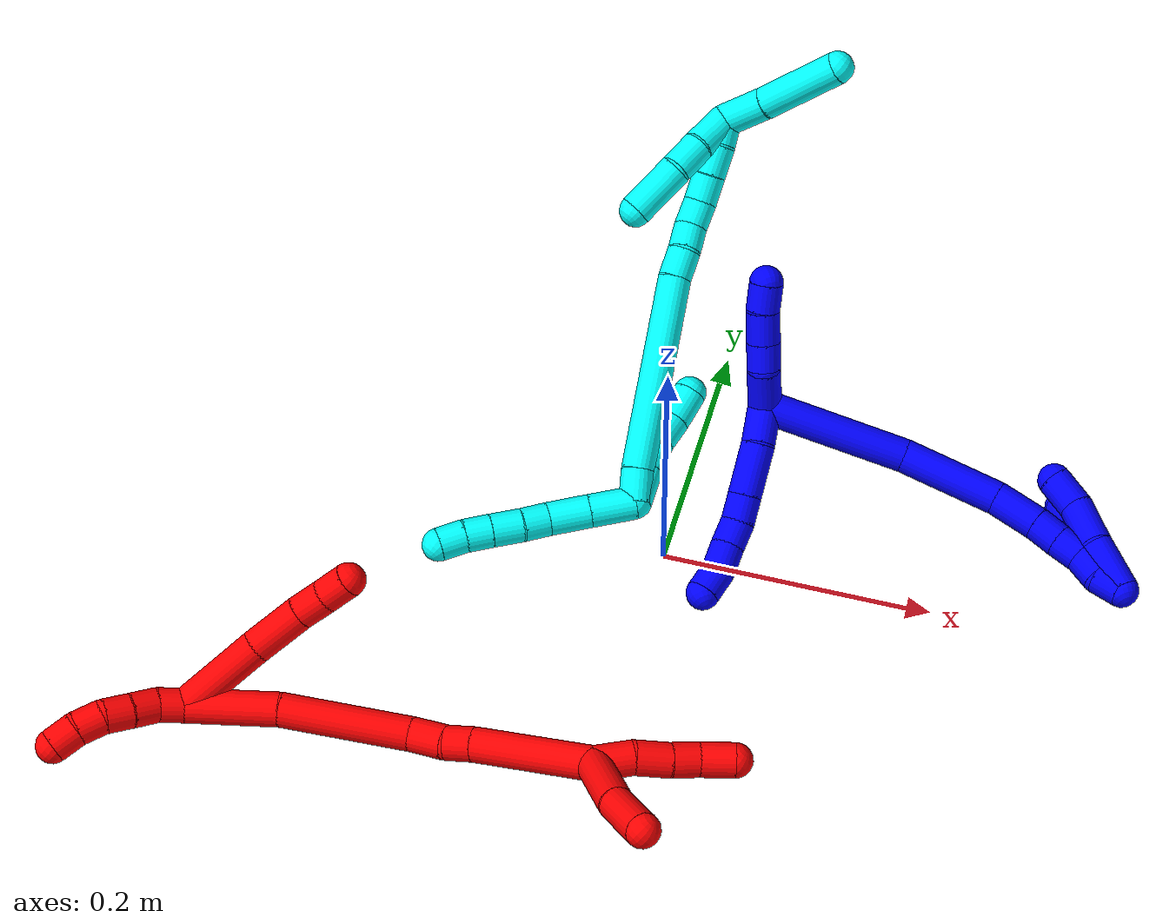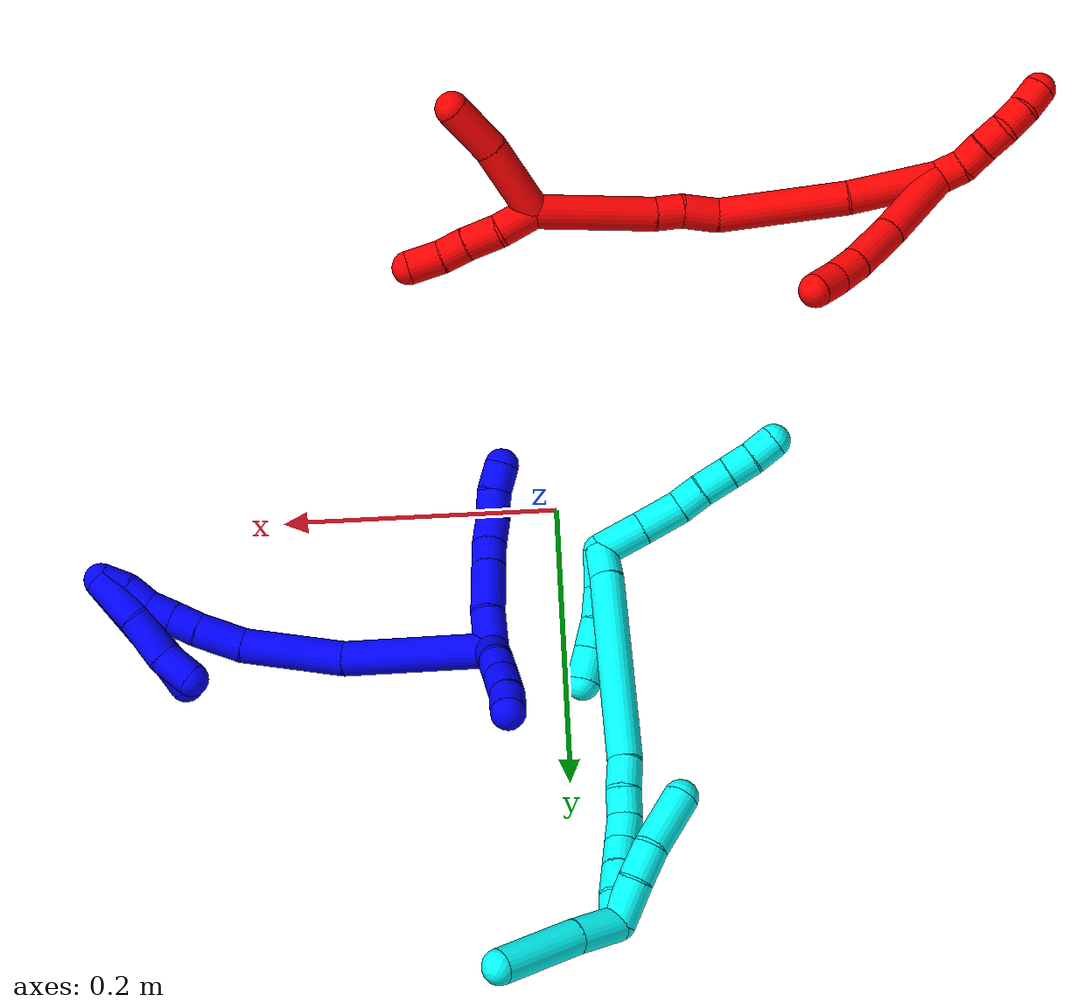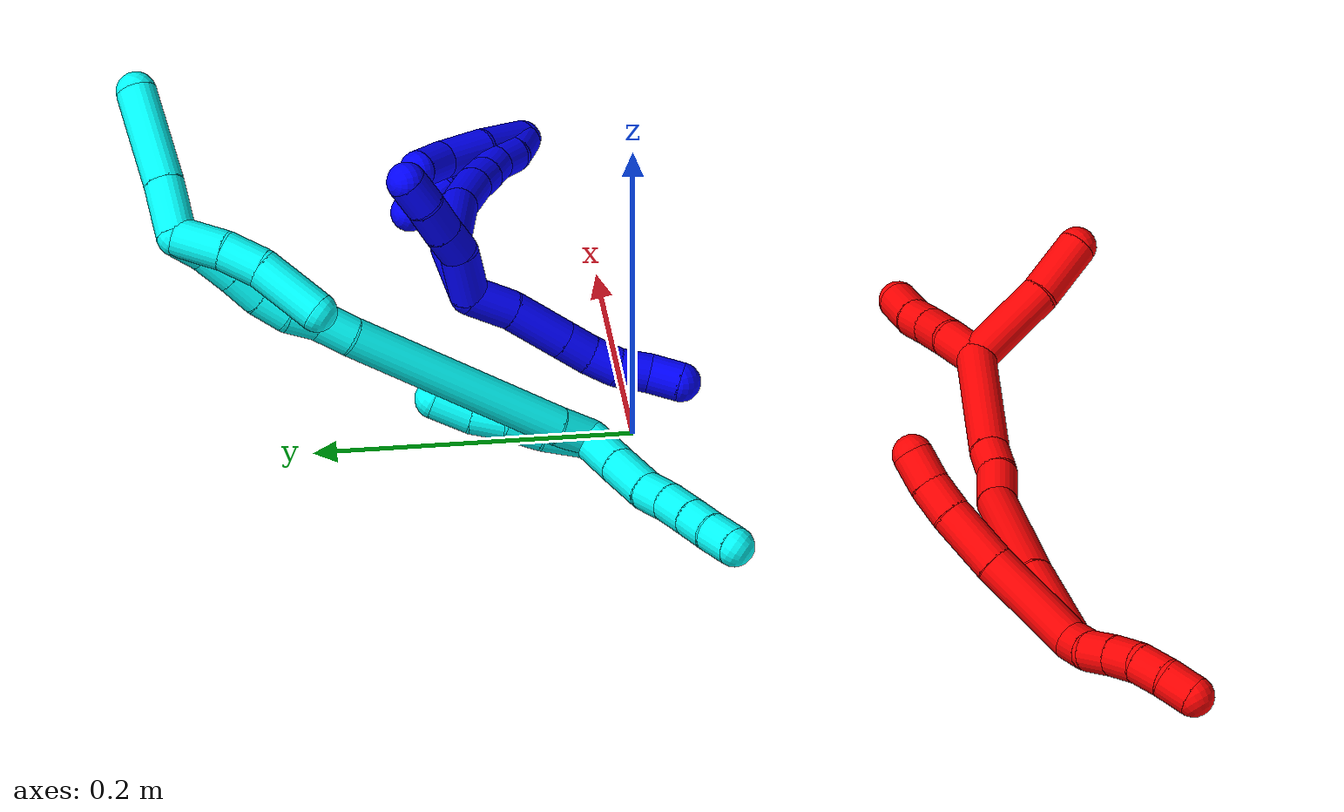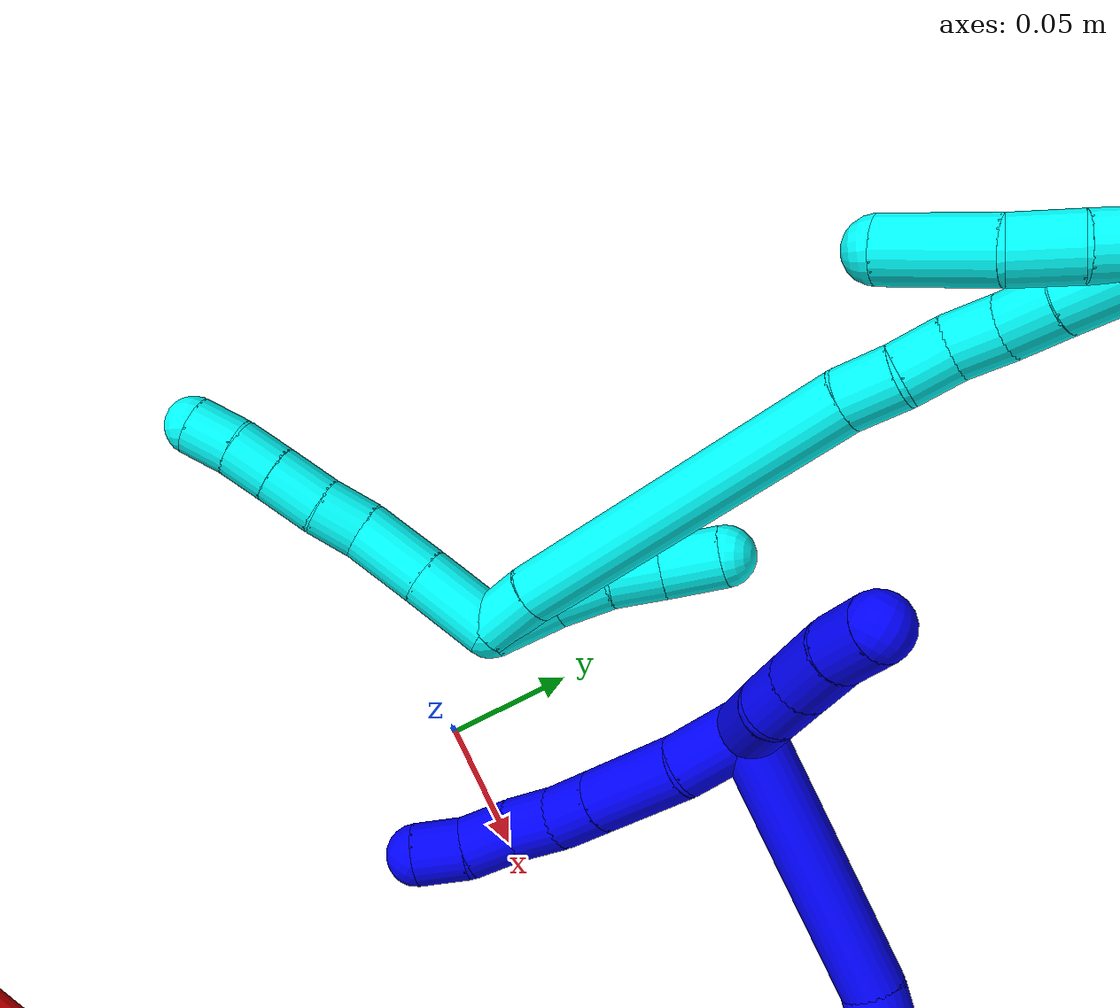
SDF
<sdf version="1.7">
 <world name="default">
  <plugin name="TubeGeneratorPlugin" filename="libtube_generator_plugin.so"/>
  <model name="photoneo_s_sensor">
   <static>1</static>
   <pose>0 0 2 1.57079 1.57079 3.14159</pose>
   <link name="link">
    <inertial><mass>0.1</mass></inertial>
    <sensor name="sensor" type="depth">
     <update_rate>30</update_rate>
     <camera>
      <horizontal_fov>1.22</horizontal_fov>
      <image><width>1920</width><height>1200</height><format>B8G8R8</format></image>
      <clip><near>0.1</near><far>4</far></clip>
      <depth_camera><output>points</output></depth_camera>
     </camera>
     <plugin name="camera_plugin" filename="libgazebo_ros_depth_camera.so">
      <baseline>0.2</baseline>
      <alwaysOn>1</alwaysOn>
      <updateRate>0.0</updateRate>
      <cameraName>camera_ir</cameraName>
      <imageTopicName>/camera/color/image_raw</imageTopicName>
      <cameraInfoTopicName>/camera/color/camera_info</cameraInfoTopicName>
      <depthImageTopicName>/camera/depth/image_raw</depthImageTopicName>
      <depthImageCameraInfoTopicName>/camera/depth/camera_info</depthImageCameraInfoTopicName>
      <pointCloudTopicName>/camera/depth/points</pointCloudTopicName>
      <frameName>fr_optical</frameName>
      <pointCloudCutoff>0.1</pointCloudCutoff>
      <pointCloudCutoffMax>2.0</pointCloudCutoffMax>
      <distortionK1>0</distortionK1>
      <distortionK2>0</distortionK2>
      <distortionK3>0</distortionK3>
      <distortionT1>0</distortionT1>
      <distortionT2>0</distortionT2>
      <CxPrime>0</CxPrime>
      <Cx>0</Cx>
      <Cy>0</Cy>
      <focalLength>0</focalLength>
      <hackBaseline>0</hackBaseline>
     </plugin>
    </sensor>
   </link>
  </model>
  <gravity>0 0 -9.8</gravity>
  <magnetic_field>6e-06 2.3e-05 -4.2e-05</magnetic_field>
  <atmosphere type="adiabatic"/>
  <physics name="default_physics" default="0" type="ode">
   <max_step_size>0.003</max_step_size>
   <real_time_factor>1</real_time_factor>
   <real_time_update_rate>1000</real_time_update_rate>
   <max_contacts>10000</max_contacts>
   <ode>
    <solver>
     <type>quick</type>
     <iters>100</iters>
     <sor>1.3</sor>
     <use_dynamic_moi_rescaling>0</use_dynamic_moi_rescaling>
    </solver>
    <constraints>
     <contact_max_correcting_vel>0</contact_max_correcting_vel>
     <contact_surface_layer>0.001</contact_surface_layer>
     <cfm>0</cfm>
     <erp>0.2</erp>
    </constraints>
   </ode>
  </physics>
  <scene><ambient>0.4 0.4 0.4 1</ambient><background>0.7 0.7 0.7 1</background><shadows>0</shadows></scene>
  <audio><device>default</device></audio>
  <spherical_coordinates>
   <surface_model>EARTH_WGS84</surface_model>
   <latitude_deg>0</latitude_deg>
   <longitude_deg>0</longitude_deg>
   <elevation>0</elevation>
   <heading_deg>0</heading_deg>
  </spherical_coordinates>
  <model name="bin">
   <static>1</static>
   <link name="bottom">
    <collision name="collision-bottom">
     <pose>0 0 -0.01 0 -0 0</pose>
     <geometry><box><size>0.8 0.6 0.02</size></box></geometry>
     <surface>
      <friction><ode><mu>100</mu><mu2>100</mu2></ode></friction>
      <contact><collide_bitmask>65535</collide_bitmask></contact>
     </surface>
    </collision>
   </link>
   <link name="west_wall">
    <collision name="collision-west_wall">
     <pose>-0.41 0 0.1 0 -0 0</pose>
     <geometry><box><size>0.02 0.6 0.2</size></box></geometry>
     <surface>
      <friction><ode><mu>100</mu><mu2>100</mu2></ode></friction>
      <contact><collide_bitmask>65535</collide_bitmask></contact>
     </surface>
    </collision>
   </link>
   <link name="east_wall">
    <collision name="collision-east_wall">
     <pose>0.41 0 0.1 0 -0 0</pose>
     <geometry><box><size>0.02 0.6 0.2</size></box></geometry>
     <surface>
      <friction><ode><mu>100</mu><mu2>100</mu2></ode></friction>
      <contact><collide_bitmask>65535</collide_bitmask></contact>
     </surface>
    </collision>
   </link>
   <link name="south_wall">
    <collision name="collision-south_wall">
     <pose>0 -0.31 0.1 0 -0 0</pose>
     <geometry><box><size>0.8 0.02 0.2</size></box></geometry>
     <surface>
      <friction><ode><mu>100</mu><mu2>100</mu2></ode></friction>
      <contact><collide_bitmask>65535</collide_bitmask></contact>
     </surface>
    </collision>
   </link>
   <link name="north_wall">
    <collision name="collision-north_wall">
     <pose>0 0.31 0.1 0 -0 0</pose>
     <geometry><box><size>0.8 0.02 0.2</size></box></geometry>
     <surface>
      <friction><ode><mu>100</mu><mu2>100</mu2></ode></friction>
      <contact><collide_bitmask>65535</collide_bitmask></contact>
     </surface>
    </collision>
   </link>
  </model>
  <model name="1">
   <static>0</static>
   <link name="1">
    <collision name="collision-cylinder-e_1_2_8">
     <pose>0.00281 -0.007584 0.012271 0.553564 0.192383 0.054806</pose>
     <geometry><cylinder><radius>0.0125</radius><length>0.029392</length></cylinder></geometry>
     <surface>
      <friction><ode><mu>1.16</mu><mu2>1.16</mu2><slip1>0</slip1><slip2>0</slip2></ode></friction>
      <contact><ode><kp>1e+06</kp><kd>1</kd><max_vel>0</max_vel><min_depth>0.001</min_depth></ode></contact>
     </surface>
    </collision>
    <visual name="visual-cylinder-e_1_2_8">
     <pose>0.00281 -0.007584 0.012271 0.553564 0.192383 0.054806</pose>
     <geometry><cylinder><radius>0.0125</radius><length>0.029392</length></cylinder></geometry>
     <material><ambient>0 0 1 1</ambient></material>
    </visual>
    <collision name="collision-cylinder-e_2_8_9">
     <pose>0.01166 -0.02677 0.03903 0.675245 0.314589 0.111246</pose>
     <geometry><cylinder><radius>0.0125</radius><length>0.039039</length></cylinder></geometry>
     <surface>
      <friction><ode><mu>1.16</mu><mu2>1.16</mu2><slip1>0</slip1><slip2>0</slip2></ode></friction>
      <contact><ode><kp>1e+06</kp><kd>1</kd><max_vel>0</max_vel><min_depth>0.001</min_depth></ode></contact>
     </surface>
    </collision>
    <visual name="visual-cylinder-e_2_8_9">
     <pose>0.01166 -0.02677 0.03903 0.675245 0.314589 0.111246</pose>
     <geometry><cylinder><radius>0.0125</radius><length>0.039039</length></cylinder></geometry>
     <material><ambient>0 0 1 1</ambient></material>
    </visual>
    <collision name="collision-cylinder-e_3_9_10">
     <pose>0.020812 -0.044347 0.060979 0.675257 0.314768 0.111312</pose>
     <geometry><cylinder><radius>0.0125</radius><length>0.020105</length></cylinder></geometry>
     <surface>
      <friction><ode><mu>1.16</mu><mu2>1.16</mu2><slip1>0</slip1><slip2>0</slip2></ode></friction>
      <contact><ode><kp>1e+06</kp><kd>1</kd><max_vel>0</max_vel><min_depth>0.001</min_depth></ode></contact>
     </surface>
    </collision>
    <visual name="visual-cylinder-e_3_9_10">
     <pose>0.020812 -0.044347 0.060979 0.675257 0.314768 0.111312</pose>
     <geometry><cylinder><radius>0.0125</radius><length>0.020105</length></cylinder></geometry>
     <material><ambient>0 0 1 1</ambient></material>
    </visual>
    <collision name="collision-cylinder-e_4_10_11">
     <pose>0.025395 -0.05728 0.0755 0.77806 0.147378 0.060504</pose>
     <geometry><cylinder><radius>0.0125</radius><length>0.020042</length></cylinder></geometry>
     <surface>
      <friction><ode><mu>1.16</mu><mu2>1.16</mu2><slip1>0</slip1><slip2>0</slip2></ode></friction>
      <contact><ode><kp>1e+06</kp><kd>1</kd><max_vel>0</max_vel><min_depth>0.001</min_depth></ode></contact>
     </surface>
    </collision>
    <visual name="visual-cylinder-e_4_10_11">
     <pose>0.025395 -0.05728 0.0755 0.77806 0.147378 0.060504</pose>
     <geometry><cylinder><radius>0.0125</radius><length>0.020042</length></cylinder></geometry>
     <material><ambient>0 0 1 1</ambient></material>
    </visual>
    <collision name="collision-cylinder-e_5_11_12">
     <pose>0.026053 -0.070544 0.090691 0.659726 -0.078968 -0.027049</pose>
     <geometry><cylinder><radius>0.0125</radius><length>0.020644</length></cylinder></geometry>
     <surface>
      <friction><ode><mu>1.16</mu><mu2>1.16</mu2><slip1>0</slip1><slip2>0</slip2></ode></friction>
      <contact><ode><kp>1e+06</kp><kd>1</kd><max_vel>0</max_vel><min_depth>0.001</min_depth></ode></contact>
     </surface>
    </collision>
    <visual name="visual-cylinder-e_5_11_12">
     <pose>0.026053 -0.070544 0.090691 0.659726 -0.078968 -0.027049</pose>
     <geometry><cylinder><radius>0.0125</radius><length>0.020644</length></cylinder></geometry>
     <material><ambient>0 0 1 1</ambient></material>
    </visual>
    <collision name="collision-cylinder-e_6_12_6">
     <pose>0.023991 -0.084865 0.105313 0.890072 -0.12032 -0.05744</pose>
     <geometry><cylinder><radius>0.0125</radius><length>0.020779</length></cylinder></geometry>
     <surface>
      <friction><ode><mu>1.16</mu><mu2>1.16</mu2><slip1>0</slip1><slip2>0</slip2></ode></friction>
      <contact><ode><kp>1e+06</kp><kd>1</kd><max_vel>0</max_vel><min_depth>0.001</min_depth></ode></contact>
     </surface>
    </collision>
    <visual name="visual-cylinder-e_6_12_6">
     <pose>0.023991 -0.084865 0.105313 0.890072 -0.12032 -0.05744</pose>
     <geometry><cylinder><radius>0.0125</radius><length>0.020779</length></cylinder></geometry>
     <material><ambient>0 0 1 1</ambient></material>
    </visual>
    <collision name="collision-cylinder-e_1_2_13">
     <pose>-0.015124 0.004598 -0.006503 -2.52616 -1.0861 2.17229</pose>
     <geometry><cylinder><radius>0.0125</radius><length>0.034186</length></cylinder></geometry>
     <surface>
      <friction><ode><mu>1.16</mu><mu2>1.16</mu2><slip1>0</slip1><slip2>0</slip2></ode></friction>
      <contact><ode><kp>1e+06</kp><kd>1</kd><max_vel>0</max_vel><min_depth>0.001</min_depth></ode></contact>
     </surface>
    </collision>
    <visual name="visual-cylinder-e_1_2_13">
     <pose>-0.015124 0.004598 -0.006503 -2.52616 -1.0861 2.17229</pose>
     <geometry><cylinder><radius>0.0125</radius><length>0.034186</length></cylinder></geometry>
     <material><ambient>0 0 1 1</ambient></material>
    </visual>
    <collision name="collision-cylinder-e_2_13_14">
     <pose>-0.037337 0.012597 -0.019593 -2.66495 -0.763026 2.05258</pose>
     <geometry><cylinder><radius>0.0125</radius><length>0.020513</length></cylinder></geometry>
     <surface>
      <friction><ode><mu>1.16</mu><mu2>1.16</mu2><slip1>0</slip1><slip2>0</slip2></ode></friction>
      <contact><ode><kp>1e+06</kp><kd>1</kd><max_vel>0</max_vel><min_depth>0.001</min_depth></ode></contact>
     </surface>
    </collision>
    <visual name="visual-cylinder-e_2_13_14">
     <pose>-0.037337 0.012597 -0.019593 -2.66495 -0.763026 2.05258</pose>
     <geometry><cylinder><radius>0.0125</radius><length>0.020513</length></cylinder></geometry>
     <material><ambient>0 0 1 1</ambient></material>
    </visual>
    <collision name="collision-cylinder-e_3_14_15">
     <pose>-0.053139 0.019966 -0.033557 -2.64814 -0.805134 2.07335</pose>
     <geometry><cylinder><radius>0.0125</radius><length>0.024175</length></cylinder></geometry>
     <surface>
      <friction><ode><mu>1.16</mu><mu2>1.16</mu2><slip1>0</slip1><slip2>0</slip2></ode></friction>
      <contact><ode><kp>1e+06</kp><kd>1</kd><max_vel>0</max_vel><min_depth>0.001</min_depth></ode></contact>
     </surface>
    </collision>
    <visual name="visual-cylinder-e_3_14_15">
     <pose>-0.053139 0.019966 -0.033557 -2.64814 -0.805134 2.07335</pose>
     <geometry><cylinder><radius>0.0125</radius><length>0.024175</length></cylinder></geometry>
     <material><ambient>0 0 1 1</ambient></material>
    </visual>
    <collision name="collision-cylinder-e_4_15_5">
     <pose>-0.0688 0.028821 -0.047214 -2.48023 -0.717651 1.65922</pose>
     <geometry><cylinder><radius>0.0125</radius><length>0.021126</length></cylinder></geometry>
     <surface>
      <friction><ode><mu>1.16</mu><mu2>1.16</mu2><slip1>0</slip1><slip2>0</slip2></ode></friction>
      <contact><ode><kp>1e+06</kp><kd>1</kd><max_vel>0</max_vel><min_depth>0.001</min_depth></ode></contact>
     </surface>
    </collision>
    <visual name="visual-cylinder-e_4_15_5">
     <pose>-0.0688 0.028821 -0.047214 -2.48023 -0.717651 1.65922</pose>
     <geometry><cylinder><radius>0.0125</radius><length>0.021126</length></cylinder></geometry>
     <material><ambient>0 0 1 1</ambient></material>
    </visual>
    <collision name="collision-cylinder-e_1_2_16">
     <pose>0.019478 0.040897 0.030407 -0.931458 0.365075 -0.185024</pose>
     <geometry><cylinder><radius>0.0125</radius><length>0.109116</length></cylinder></geometry>
     <surface>
      <friction><ode><mu>1.16</mu><mu2>1.16</mu2><slip1>0</slip1><slip2>0</slip2></ode></friction>
      <contact><ode><kp>1e+06</kp><kd>1</kd><max_vel>0</max_vel><min_depth>0.001</min_depth></ode></contact>
     </surface>
    </collision>
    <visual name="visual-cylinder-e_1_2_16">
     <pose>0.019478 0.040897 0.030407 -0.931458 0.365075 -0.185024</pose>
     <geometry><cylinder><radius>0.0125</radius><length>0.109116</length></cylinder></geometry>
     <material><ambient>0 0 1 1</ambient></material>
    </visual>
    <collision name="collision-cylinder-e_2_16_17">
     <pose>0.047414 0.107274 0.086957 -0.772591 0.22766 -0.092931</pose>
     <geometry><cylinder><radius>0.0125</radius><length>0.074945</length></cylinder></geometry>
     <surface>
      <friction><ode><mu>1.16</mu><mu2>1.16</mu2><slip1>0</slip1><slip2>0</slip2></ode></friction>
      <contact><ode><kp>1e+06</kp><kd>1</kd><max_vel>0</max_vel><min_depth>0.001</min_depth></ode></contact>
     </surface>
    </collision>
    <visual name="visual-cylinder-e_2_16_17">
     <pose>0.047414 0.107274 0.086957 -0.772591 0.22766 -0.092931</pose>
     <geometry><cylinder><radius>0.0125</radius><length>0.074945</length></cylinder></geometry>
     <material><ambient>0 0 1 1</ambient></material>
    </visual>
    <collision name="collision-cylinder-e_3_17_18">
     <pose>0.058086 0.142483 0.12752 -0.593431 0.126649 -0.038769</pose>
     <geometry><cylinder><radius>0.0125</radius><length>0.035072</length></cylinder></geometry>
     <surface>
      <friction><ode><mu>1.16</mu><mu2>1.16</mu2><slip1>0</slip1><slip2>0</slip2></ode></friction>
      <contact><ode><kp>1e+06</kp><kd>1</kd><max_vel>0</max_vel><min_depth>0.001</min_depth></ode></contact>
     </surface>
    </collision>
    <visual name="visual-cylinder-e_3_17_18">
     <pose>0.058086 0.142483 0.12752 -0.593431 0.126649 -0.038769</pose>
     <geometry><cylinder><radius>0.0125</radius><length>0.035072</length></cylinder></geometry>
     <material><ambient>0 0 1 1</ambient></material>
    </visual>
    <collision name="collision-cylinder-e_4_18_19">
     <pose>0.061574 0.15703 0.150947 -0.491346 0.123982 -0.031124</pose>
     <geometry><cylinder><radius>0.0125</radius><length>0.020586</length></cylinder></geometry>
     <surface>
      <friction><ode><mu>1.16</mu><mu2>1.16</mu2><slip1>0</slip1><slip2>0</slip2></ode></friction>
      <contact><ode><kp>1e+06</kp><kd>1</kd><max_vel>0</max_vel><min_depth>0.001</min_depth></ode></contact>
     </surface>
    </collision>
    <visual name="visual-cylinder-e_4_18_19">
     <pose>0.061574 0.15703 0.150947 -0.491346 0.123982 -0.031124</pose>
     <geometry><cylinder><radius>0.0125</radius><length>0.020586</length></cylinder></geometry>
     <material><ambient>0 0 1 1</ambient></material>
    </visual>
    <collision name="collision-cylinder-e_5_19_20">
     <pose>0.063546 0.166853 0.16865 -0.522115 0.069497 -0.018573</pose>
     <geometry><cylinder><radius>0.0125</radius><length>0.020118</length></cylinder></geometry>
     <surface>
      <friction><ode><mu>1.16</mu><mu2>1.16</mu2><slip1>0</slip1><slip2>0</slip2></ode></friction>
      <contact><ode><kp>1e+06</kp><kd>1</kd><max_vel>0</max_vel><min_depth>0.001</min_depth></ode></contact>
     </surface>
    </collision>
    <visual name="visual-cylinder-e_5_19_20">
     <pose>0.063546 0.166853 0.16865 -0.522115 0.069497 -0.018573</pose>
     <geometry><cylinder><radius>0.0125</radius><length>0.020118</length></cylinder></geometry>
     <material><ambient>0 0 1 1</ambient></material>
    </visual>
    <collision name="collision-cylinder-e_6_20_21">
     <pose>0.064473 0.174454 0.187035 -0.261903 0.022851 -0.00301</pose>
     <geometry><cylinder><radius>0.0125</radius><length>0.020064</length></cylinder></geometry>
     <surface>
      <friction><ode><mu>1.16</mu><mu2>1.16</mu2><slip1>0</slip1><slip2>0</slip2></ode></friction>
      <contact><ode><kp>1e+06</kp><kd>1</kd><max_vel>0</max_vel><min_depth>0.001</min_depth></ode></contact>
     </surface>
    </collision>
    <visual name="visual-cylinder-e_6_20_21">
     <pose>0.064473 0.174454 0.187035 -0.261903 0.022851 -0.00301</pose>
     <geometry><cylinder><radius>0.0125</radius><length>0.020064</length></cylinder></geometry>
     <material><ambient>0 0 1 1</ambient></material>
    </visual>
    <collision name="collision-cylinder-e_7_21_1">
     <pose>0.064745 0.182688 0.205042 -0.595477 0.004241 -0.001302</pose>
     <geometry><cylinder><radius>0.0125</radius><length>0.0201</length></cylinder></geometry>
     <surface>
      <friction><ode><mu>1.16</mu><mu2>1.16</mu2><slip1>0</slip1><slip2>0</slip2></ode></friction>
      <contact><ode><kp>1e+06</kp><kd>1</kd><max_vel>0</max_vel><min_depth>0.001</min_depth></ode></contact>
     </surface>
    </collision>
    <visual name="visual-cylinder-e_7_21_1">
     <pose>0.064745 0.182688 0.205042 -0.595477 0.004241 -0.001302</pose>
     <geometry><cylinder><radius>0.0125</radius><length>0.0201</length></cylinder></geometry>
     <material><ambient>0 0 1 1</ambient></material>
    </visual>
    <collision name="collision-cylinder-e_1_1_22">
     <pose>0.062748 0.186413 0.193969 3.04331 -0.104282 -1.63009</pose>
     <geometry><cylinder><radius>0.0125</radius><length>0.039188</length></cylinder></geometry>
     <surface>
      <friction><ode><mu>1.16</mu><mu2>1.16</mu2><slip1>0</slip1><slip2>0</slip2></ode></friction>
      <contact><ode><kp>1e+06</kp><kd>1</kd><max_vel>0</max_vel><min_depth>0.001</min_depth></ode></contact>
     </surface>
    </collision>
    <visual name="visual-cylinder-e_1_1_22">
     <pose>0.062748 0.186413 0.193969 3.04331 -0.104282 -1.63009</pose>
     <geometry><cylinder><radius>0.0125</radius><length>0.039188</length></cylinder></geometry>
     <material><ambient>0 0 1 1</ambient></material>
    </visual>
    <collision name="collision-cylinder-e_2_22_23">
     <pose>0.061857 0.184059 0.157352 3.11598 0.066536 2.40683</pose>
     <geometry><cylinder><radius>0.0125</radius><length>0.034534</length></cylinder></geometry>
     <surface>
      <friction><ode><mu>1.16</mu><mu2>1.16</mu2><slip1>0</slip1><slip2>0</slip2></ode></friction>
      <contact><ode><kp>1e+06</kp><kd>1</kd><max_vel>0</max_vel><min_depth>0.001</min_depth></ode></contact>
     </surface>
    </collision>
    <visual name="visual-cylinder-e_2_22_23">
     <pose>0.061857 0.184059 0.157352 3.11598 0.066536 2.40683</pose>
     <geometry><cylinder><radius>0.0125</radius><length>0.034534</length></cylinder></geometry>
     <material><ambient>0 0 1 1</ambient></material>
    </visual>
    <collision name="collision-cylinder-e_3_23_4">
     <pose>0.061732 0.180361 0.127464 2.8899 -0.097039 -0.732945</pose>
     <geometry><cylinder><radius>0.0125</radius><length>0.026278</length></cylinder></geometry>
     <surface>
      <friction><ode><mu>1.16</mu><mu2>1.16</mu2><slip1>0</slip1><slip2>0</slip2></ode></friction>
      <contact><ode><kp>1e+06</kp><kd>1</kd><max_vel>0</max_vel><min_depth>0.001</min_depth></ode></contact>
     </surface>
    </collision>
    <visual name="visual-cylinder-e_3_23_4">
     <pose>0.061732 0.180361 0.127464 2.8899 -0.097039 -0.732945</pose>
     <geometry><cylinder><radius>0.0125</radius><length>0.026278</length></cylinder></geometry>
     <material><ambient>0 0 1 1</ambient></material>
    </visual>
    <collision name="collision-cylinder-e_1_1_24">
     <pose>0.073096 0.184047 0.17984 3.01465 0.241078 2.17516</pose>
     <geometry><cylinder><radius>0.0125</radius><length>0.069601</length></cylinder></geometry>
     <surface>
      <friction><ode><mu>1.16</mu><mu2>1.16</mu2><slip1>0</slip1><slip2>0</slip2></ode></friction>
      <contact><ode><kp>1e+06</kp><kd>1</kd><max_vel>0</max_vel><min_depth>0.001</min_depth></ode></contact>
     </surface>
    </collision>
    <visual name="visual-cylinder-e_1_1_24">
     <pose>0.073096 0.184047 0.17984 3.01465 0.241078 2.17516</pose>
     <geometry><cylinder><radius>0.0125</radius><length>0.069601</length></cylinder></geometry>
     <material><ambient>0 0 1 1</ambient></material>
    </visual>
    <collision name="collision-cylinder-e_2_24_3">
     <pose>0.089376 0.178394 0.13345 3.03521 0.552061 2.77002</pose>
     <geometry><cylinder><radius>0.0125</radius><length>0.030399</length></cylinder></geometry>
     <surface>
      <friction><ode><mu>1.16</mu><mu2>1.16</mu2><slip1>0</slip1><slip2>0</slip2></ode></friction>
      <contact><ode><kp>1e+06</kp><kd>1</kd><max_vel>0</max_vel><min_depth>0.001</min_depth></ode></contact>
     </surface>
    </collision>
    <visual name="visual-cylinder-e_2_24_3">
     <pose>0.089376 0.178394 0.13345 3.03521 0.552061 2.77002</pose>
     <geometry><cylinder><radius>0.0125</radius><length>0.030399</length></cylinder></geometry>
     <material><ambient>0 0 1 1</ambient></material>
    </visual>
    <collision name="collision-sphere-3">
     <pose>0.097348 0.17702 0.120581 0 -0 0</pose>
     <geometry><sphere><radius>0.0125</radius></sphere></geometry>
     <surface>
      <friction><ode><mu>1.16</mu><mu2>1.16</mu2><slip1>0</slip1><slip2>0</slip2></ode></friction>
      <contact><ode><kp>1e+06</kp><kd>1</kd><max_vel>0</max_vel><min_depth>0.001</min_depth></ode></contact>
     </surface>
    </collision>
    <visual name="visual-sphere-3">
     <pose>0.097348 0.17702 0.120581 0 -0 0</pose>
     <geometry><sphere><radius>0.0125</radius></sphere></geometry>
     <material><ambient>0 0 1 1</ambient></material>
    </visual>
    <collision name="collision-sphere-24">
     <pose>0.081405 0.179768 0.146318 0 -0 0</pose>
     <geometry><sphere><radius>0.0125</radius></sphere></geometry>
     <surface>
      <friction><ode><mu>1.16</mu><mu2>1.16</mu2><slip1>0</slip1><slip2>0</slip2></ode></friction>
      <contact><ode><kp>1e+06</kp><kd>1</kd><max_vel>0</max_vel><min_depth>0.001</min_depth></ode></contact>
     </surface>
    </collision>
    <visual name="visual-sphere-24">
     <pose>0.081405 0.179768 0.146318 0 -0 0</pose>
     <geometry><sphere><radius>0.0125</radius></sphere></geometry>
     <material><ambient>0 0 1 1</ambient></material>
    </visual>
    <collision name="collision-sphere-4">
     <pose>0.060459 0.177104 0.114799 0 -0 0</pose>
     <geometry><sphere><radius>0.0125</radius></sphere></geometry>
     <surface>
      <friction><ode><mu>1.16</mu><mu2>1.16</mu2><slip1>0</slip1><slip2>0</slip2></ode></friction>
      <contact><ode><kp>1e+06</kp><kd>1</kd><max_vel>0</max_vel><min_depth>0.001</min_depth></ode></contact>
     </surface>
    </collision>
    <visual name="visual-sphere-4">
     <pose>0.060459 0.177104 0.114799 0 -0 0</pose>
     <geometry><sphere><radius>0.0125</radius></sphere></geometry>
     <material><ambient>0 0 1 1</ambient></material>
    </visual>
    <collision name="collision-sphere-23">
     <pose>0.063005 0.183618 0.140129 0 -0 0</pose>
     <geometry><sphere><radius>0.0125</radius></sphere></geometry>
     <surface>
      <friction><ode><mu>1.16</mu><mu2>1.16</mu2><slip1>0</slip1><slip2>0</slip2></ode></friction>
      <contact><ode><kp>1e+06</kp><kd>1</kd><max_vel>0</max_vel><min_depth>0.001</min_depth></ode></contact>
     </surface>
    </collision>
    <visual name="visual-sphere-23">
     <pose>0.063005 0.183618 0.140129 0 -0 0</pose>
     <geometry><sphere><radius>0.0125</radius></sphere></geometry>
     <material><ambient>0 0 1 1</ambient></material>
    </visual>
    <collision name="collision-sphere-22">
     <pose>0.060709 0.1845 0.174575 0 -0 0</pose>
     <geometry><sphere><radius>0.0125</radius></sphere></geometry>
     <surface>
      <friction><ode><mu>1.16</mu><mu2>1.16</mu2><slip1>0</slip1><slip2>0</slip2></ode></friction>
      <contact><ode><kp>1e+06</kp><kd>1</kd><max_vel>0</max_vel><min_depth>0.001</min_depth></ode></contact>
     </surface>
    </collision>
    <visual name="visual-sphere-22">
     <pose>0.060709 0.1845 0.174575 0 -0 0</pose>
     <geometry><sphere><radius>0.0125</radius></sphere></geometry>
     <material><ambient>0 0 1 1</ambient></material>
    </visual>
    <collision name="collision-sphere-1">
     <pose>0.064788 0.188325 0.213362 0 -0 0</pose>
     <geometry><sphere><radius>0.0125</radius></sphere></geometry>
     <surface>
      <friction><ode><mu>1.16</mu><mu2>1.16</mu2><slip1>0</slip1><slip2>0</slip2></ode></friction>
      <contact><ode><kp>1e+06</kp><kd>1</kd><max_vel>0</max_vel><min_depth>0.001</min_depth></ode></contact>
     </surface>
    </collision>
    <visual name="visual-sphere-1">
     <pose>0.064788 0.188325 0.213362 0 -0 0</pose>
     <geometry><sphere><radius>0.0125</radius></sphere></geometry>
     <material><ambient>0 0 1 1</ambient></material>
    </visual>
    <collision name="collision-sphere-21">
     <pose>0.064703 0.177051 0.196722 0 -0 0</pose>
     <geometry><sphere><radius>0.0125</radius></sphere></geometry>
     <surface>
      <friction><ode><mu>1.16</mu><mu2>1.16</mu2><slip1>0</slip1><slip2>0</slip2></ode></friction>
      <contact><ode><kp>1e+06</kp><kd>1</kd><max_vel>0</max_vel><min_depth>0.001</min_depth></ode></contact>
     </surface>
    </collision>
    <visual name="visual-sphere-21">
     <pose>0.064703 0.177051 0.196722 0 -0 0</pose>
     <geometry><sphere><radius>0.0125</radius></sphere></geometry>
     <material><ambient>0 0 1 1</ambient></material>
    </visual>
    <collision name="collision-sphere-12">
     <pose>0.025238 -0.07685 0.098821 0 -0 0</pose>
     <geometry><sphere><radius>0.0125</radius></sphere></geometry>
     <surface>
      <friction><ode><mu>1.16</mu><mu2>1.16</mu2><slip1>0</slip1><slip2>0</slip2></ode></friction>
      <contact><ode><kp>1e+06</kp><kd>1</kd><max_vel>0</max_vel><min_depth>0.001</min_depth></ode></contact>
     </surface>
    </collision>
    <visual name="visual-sphere-12">
     <pose>0.025238 -0.07685 0.098821 0 -0 0</pose>
     <geometry><sphere><radius>0.0125</radius></sphere></geometry>
     <material><ambient>0 0 1 1</ambient></material>
    </visual>
    <collision name="collision-sphere-11">
     <pose>0.026867 -0.064237 0.08256 0 -0 0</pose>
     <geometry><sphere><radius>0.0125</radius></sphere></geometry>
     <surface>
      <friction><ode><mu>1.16</mu><mu2>1.16</mu2><slip1>0</slip1><slip2>0</slip2></ode></friction>
      <contact><ode><kp>1e+06</kp><kd>1</kd><max_vel>0</max_vel><min_depth>0.001</min_depth></ode></contact>
     </surface>
    </collision>
    <visual name="visual-sphere-11">
     <pose>0.026867 -0.064237 0.08256 0 -0 0</pose>
     <geometry><sphere><radius>0.0125</radius></sphere></geometry>
     <material><ambient>0 0 1 1</ambient></material>
    </visual>
    <collision name="collision-sphere-10">
     <pose>0.023924 -0.050322 0.06844 0 -0 0</pose>
     <geometry><sphere><radius>0.0125</radius></sphere></geometry>
     <surface>
      <friction><ode><mu>1.16</mu><mu2>1.16</mu2><slip1>0</slip1><slip2>0</slip2></ode></friction>
      <contact><ode><kp>1e+06</kp><kd>1</kd><max_vel>0</max_vel><min_depth>0.001</min_depth></ode></contact>
     </surface>
    </collision>
    <visual name="visual-sphere-10">
     <pose>0.023924 -0.050322 0.06844 0 -0 0</pose>
     <geometry><sphere><radius>0.0125</radius></sphere></geometry>
     <material><ambient>0 0 1 1</ambient></material>
    </visual>
    <collision name="collision-sphere-9">
     <pose>0.017699 -0.038372 0.053518 0 -0 0</pose>
     <geometry><sphere><radius>0.0125</radius></sphere></geometry>
     <surface>
      <friction><ode><mu>1.16</mu><mu2>1.16</mu2><slip1>0</slip1><slip2>0</slip2></ode></friction>
      <contact><ode><kp>1e+06</kp><kd>1</kd><max_vel>0</max_vel><min_depth>0.001</min_depth></ode></contact>
     </surface>
    </collision>
    <visual name="visual-sphere-9">
     <pose>0.017699 -0.038372 0.053518 0 -0 0</pose>
     <geometry><sphere><radius>0.0125</radius></sphere></geometry>
     <material><ambient>0 0 1 1</ambient></material>
    </visual>
    <collision name="collision-sphere-2">
     <geometry><sphere><radius>0.0125</radius></sphere></geometry>
     <surface>
      <friction><ode><mu>1.16</mu><mu2>1.16</mu2><slip1>0</slip1><slip2>0</slip2></ode></friction>
      <contact><ode><kp>1e+06</kp><kd>1</kd><max_vel>0</max_vel><min_depth>0.001</min_depth></ode></contact>
     </surface>
    </collision>
    <visual name="visual-sphere-2">
     <geometry><sphere><radius>0.0125</radius></sphere></geometry>
     <material><ambient>0 0 1 1</ambient></material>
    </visual>
    <collision name="collision-sphere-19">
     <pose>0.062847 0.161849 0.159952 0 -0 0</pose>
     <geometry><sphere><radius>0.0125</radius></sphere></geometry>
     <surface>
      <friction><ode><mu>1.16</mu><mu2>1.16</mu2><slip1>0</slip1><slip2>0</slip2></ode></friction>
      <contact><ode><kp>1e+06</kp><kd>1</kd><max_vel>0</max_vel><min_depth>0.001</min_depth></ode></contact>
     </surface>
    </collision>
    <visual name="visual-sphere-19">
     <pose>0.062847 0.161849 0.159952 0 -0 0</pose>
     <geometry><sphere><radius>0.0125</radius></sphere></geometry>
     <material><ambient>0 0 1 1</ambient></material>
    </visual>
    <collision name="collision-sphere-8">
     <pose>0.00562 -0.015167 0.024541 0 -0 0</pose>
     <geometry><sphere><radius>0.0125</radius></sphere></geometry>
     <surface>
      <friction><ode><mu>1.16</mu><mu2>1.16</mu2><slip1>0</slip1><slip2>0</slip2></ode></friction>
      <contact><ode><kp>1e+06</kp><kd>1</kd><max_vel>0</max_vel><min_depth>0.001</min_depth></ode></contact>
     </surface>
    </collision>
    <visual name="visual-sphere-8">
     <pose>0.00562 -0.015167 0.024541 0 -0 0</pose>
     <geometry><sphere><radius>0.0125</radius></sphere></geometry>
     <material><ambient>0 0 1 1</ambient></material>
    </visual>
    <collision name="collision-sphere-6">
     <pose>0.022744 -0.092881 0.111804 0 -0 0</pose>
     <geometry><sphere><radius>0.0125</radius></sphere></geometry>
     <surface>
      <friction><ode><mu>1.16</mu><mu2>1.16</mu2><slip1>0</slip1><slip2>0</slip2></ode></friction>
      <contact><ode><kp>1e+06</kp><kd>1</kd><max_vel>0</max_vel><min_depth>0.001</min_depth></ode></contact>
     </surface>
    </collision>
    <visual name="visual-sphere-6">
     <pose>0.022744 -0.092881 0.111804 0 -0 0</pose>
     <geometry><sphere><radius>0.0125</radius></sphere></geometry>
     <material><ambient>0 0 1 1</ambient></material>
    </visual>
    <collision name="collision-sphere-13">
     <pose>-0.030248 0.009196 -0.013006 0 -0 0</pose>
     <geometry><sphere><radius>0.0125</radius></sphere></geometry>
     <surface>
      <friction><ode><mu>1.16</mu><mu2>1.16</mu2><slip1>0</slip1><slip2>0</slip2></ode></friction>
      <contact><ode><kp>1e+06</kp><kd>1</kd><max_vel>0</max_vel><min_depth>0.001</min_depth></ode></contact>
     </surface>
    </collision>
    <visual name="visual-sphere-13">
     <pose>-0.030248 0.009196 -0.013006 0 -0 0</pose>
     <geometry><sphere><radius>0.0125</radius></sphere></geometry>
     <material><ambient>0 0 1 1</ambient></material>
    </visual>
    <collision name="collision-sphere-14">
     <pose>-0.044425 0.015998 -0.026179 0 -0 0</pose>
     <geometry><sphere><radius>0.0125</radius></sphere></geometry>
     <surface>
      <friction><ode><mu>1.16</mu><mu2>1.16</mu2><slip1>0</slip1><slip2>0</slip2></ode></friction>
      <contact><ode><kp>1e+06</kp><kd>1</kd><max_vel>0</max_vel><min_depth>0.001</min_depth></ode></contact>
     </surface>
    </collision>
    <visual name="visual-sphere-14">
     <pose>-0.044425 0.015998 -0.026179 0 -0 0</pose>
     <geometry><sphere><radius>0.0125</radius></sphere></geometry>
     <material><ambient>0 0 1 1</ambient></material>
    </visual>
    <collision name="collision-sphere-15">
     <pose>-0.061853 0.023933 -0.040934 0 -0 0</pose>
     <geometry><sphere><radius>0.0125</radius></sphere></geometry>
     <surface>
      <friction><ode><mu>1.16</mu><mu2>1.16</mu2><slip1>0</slip1><slip2>0</slip2></ode></friction>
      <contact><ode><kp>1e+06</kp><kd>1</kd><max_vel>0</max_vel><min_depth>0.001</min_depth></ode></contact>
     </surface>
    </collision>
    <visual name="visual-sphere-15">
     <pose>-0.061853 0.023933 -0.040934 0 -0 0</pose>
     <geometry><sphere><radius>0.0125</radius></sphere></geometry>
     <material><ambient>0 0 1 1</ambient></material>
    </visual>
    <collision name="collision-sphere-5">
     <pose>-0.075746 0.033709 -0.053494 0 -0 0</pose>
     <geometry><sphere><radius>0.0125</radius></sphere></geometry>
     <surface>
      <friction><ode><mu>1.16</mu><mu2>1.16</mu2><slip1>0</slip1><slip2>0</slip2></ode></friction>
      <contact><ode><kp>1e+06</kp><kd>1</kd><max_vel>0</max_vel><min_depth>0.001</min_depth></ode></contact>
     </surface>
    </collision>
    <visual name="visual-sphere-5">
     <pose>-0.075746 0.033709 -0.053494 0 -0 0</pose>
     <geometry><sphere><radius>0.0125</radius></sphere></geometry>
     <material><ambient>0 0 1 1</ambient></material>
    </visual>
    <collision name="collision-sphere-16">
     <pose>0.038956 0.081794 0.060815 0 -0 0</pose>
     <geometry><sphere><radius>0.0125</radius></sphere></geometry>
     <surface>
      <friction><ode><mu>1.16</mu><mu2>1.16</mu2><slip1>0</slip1><slip2>0</slip2></ode></friction>
      <contact><ode><kp>1e+06</kp><kd>1</kd><max_vel>0</max_vel><min_depth>0.001</min_depth></ode></contact>
     </surface>
    </collision>
    <visual name="visual-sphere-16">
     <pose>0.038956 0.081794 0.060815 0 -0 0</pose>
     <geometry><sphere><radius>0.0125</radius></sphere></geometry>
     <material><ambient>0 0 1 1</ambient></material>
    </visual>
    <collision name="collision-sphere-17">
     <pose>0.055871 0.132755 0.113098 0 -0 0</pose>
     <geometry><sphere><radius>0.0125</radius></sphere></geometry>
     <surface>
      <friction><ode><mu>1.16</mu><mu2>1.16</mu2><slip1>0</slip1><slip2>0</slip2></ode></friction>
      <contact><ode><kp>1e+06</kp><kd>1</kd><max_vel>0</max_vel><min_depth>0.001</min_depth></ode></contact>
     </surface>
    </collision>
    <visual name="visual-sphere-17">
     <pose>0.055871 0.132755 0.113098 0 -0 0</pose>
     <geometry><sphere><radius>0.0125</radius></sphere></geometry>
     <material><ambient>0 0 1 1</ambient></material>
    </visual>
    <collision name="collision-sphere-18">
     <pose>0.060301 0.152211 0.141941 0 -0 0</pose>
     <geometry><sphere><radius>0.0125</radius></sphere></geometry>
     <surface>
      <friction><ode><mu>1.16</mu><mu2>1.16</mu2><slip1>0</slip1><slip2>0</slip2></ode></friction>
      <contact><ode><kp>1e+06</kp><kd>1</kd><max_vel>0</max_vel><min_depth>0.001</min_depth></ode></contact>
     </surface>
    </collision>
    <visual name="visual-sphere-18">
     <pose>0.060301 0.152211 0.141941 0 -0 0</pose>
     <geometry><sphere><radius>0.0125</radius></sphere></geometry>
     <material><ambient>0 0 1 1</ambient></material>
    </visual>
    <collision name="collision-sphere-20">
     <pose>0.064244 0.171857 0.177348 0 -0 0</pose>
     <geometry><sphere><radius>0.0125</radius></sphere></geometry>
     <surface>
      <friction><ode><mu>1.16</mu><mu2>1.16</mu2><slip1>0</slip1><slip2>0</slip2></ode></friction>
      <contact><ode><kp>1e+06</kp><kd>1</kd><max_vel>0</max_vel><min_depth>0.001</min_depth></ode></contact>
     </surface>
    </collision>
    <visual name="visual-sphere-20">
     <pose>0.064244 0.171857 0.177348 0 -0 0</pose>
     <geometry><sphere><radius>0.0125</radius></sphere></geometry>
     <material><ambient>0 0 1 1</ambient></material>
    </visual>
    <inertial>
     <pose>0.033812 0.083833 0.090521 0 -0 0</pose>
     <mass>0.75</mass>
     <inertia>
      <ixx>0.000149</ixx>
      <ixy>0</ixy>
      <ixz>0</ixz>
      <iyy>0.000165</iyy>
      <iyz>0</iyz>
      <izz>-0.000151</izz>
     </inertia>
    </inertial>
   </link>
   <pose>0.050786 0.096536 0.07723 2.13569 1.25132 1.13047</pose>
  </model>
  <model name="2">
   <static>0</static>
   <link name="2">
    <collision name="collision-cylinder-e_1_2_8">
     <pose>0.00535 -0.008176 -0.031438 2.88716 0.163224 1.13789</pose>
     <geometry><cylinder><radius>0.0125</radius><length>0.065843</length></cylinder></geometry>
     <surface>
      <friction><ode><mu>1.16</mu><mu2>1.16</mu2><slip1>0</slip1><slip2>0</slip2></ode></friction>
      <contact><ode><kp>1e+06</kp><kd>1</kd><max_vel>0</max_vel><min_depth>0.001</min_depth></ode></contact>
     </surface>
    </collision>
    <visual name="visual-cylinder-e_1_2_8">
     <pose>0.00535 -0.008176 -0.031438 2.88716 0.163224 1.13789</pose>
     <geometry><cylinder><radius>0.0125</radius><length>0.065843</length></cylinder></geometry>
     <material><ambient>1 0 0 1</ambient></material>
    </visual>
    <collision name="collision-cylinder-e_2_8_9">
     <pose>0.014407 -0.020025 -0.082184 2.95359 0.186436 1.56238</pose>
     <geometry><cylinder><radius>0.0125</radius><length>0.040002</length></cylinder></geometry>
     <surface>
      <friction><ode><mu>1.16</mu><mu2>1.16</mu2><slip1>0</slip1><slip2>0</slip2></ode></friction>
      <contact><ode><kp>1e+06</kp><kd>1</kd><max_vel>0</max_vel><min_depth>0.001</min_depth></ode></contact>
     </surface>
    </collision>
    <visual name="visual-cylinder-e_2_8_9">
     <pose>0.014407 -0.020025 -0.082184 2.95359 0.186436 1.56238</pose>
     <geometry><cylinder><radius>0.0125</radius><length>0.040002</length></cylinder></geometry>
     <material><ambient>1 0 0 1</ambient></material>
    </visual>
    <collision name="collision-cylinder-e_3_9_10">
     <pose>0.02077 -0.024757 -0.112299 3.04394 0.239926 2.37132</pose>
     <geometry><cylinder><radius>0.0125</radius><length>0.022357</length></cylinder></geometry>
     <surface>
      <friction><ode><mu>1.16</mu><mu2>1.16</mu2><slip1>0</slip1><slip2>0</slip2></ode></friction>
      <contact><ode><kp>1e+06</kp><kd>1</kd><max_vel>0</max_vel><min_depth>0.001</min_depth></ode></contact>
     </surface>
    </collision>
    <visual name="visual-cylinder-e_3_9_10">
     <pose>0.02077 -0.024757 -0.112299 3.04394 0.239926 2.37132</pose>
     <geometry><cylinder><radius>0.0125</radius><length>0.022357</length></cylinder></geometry>
     <material><ambient>1 0 0 1</ambient></material>
    </visual>
    <collision name="collision-cylinder-e_4_10_6">
     <pose>0.025519 -0.025554 -0.133799 -3.11707 0.19312 -2.88977</pose>
     <geometry><cylinder><radius>0.0125</radius><length>0.021799</length></cylinder></geometry>
     <surface>
      <friction><ode><mu>1.16</mu><mu2>1.16</mu2><slip1>0</slip1><slip2>0</slip2></ode></friction>
      <contact><ode><kp>1e+06</kp><kd>1</kd><max_vel>0</max_vel><min_depth>0.001</min_depth></ode></contact>
     </surface>
    </collision>
    <visual name="visual-cylinder-e_4_10_6">
     <pose>0.025519 -0.025554 -0.133799 -3.11707 0.19312 -2.88977</pose>
     <geometry><cylinder><radius>0.0125</radius><length>0.021799</length></cylinder></geometry>
     <material><ambient>1 0 0 1</ambient></material>
    </visual>
    <collision name="collision-cylinder-e_1_2_11">
     <pose>-0.00798 0.002783 0.005346 -0.479869 -0.923891 0.242413</pose>
     <geometry><cylinder><radius>0.0125</radius><length>0.02</length></cylinder></geometry>
     <surface>
      <friction><ode><mu>1.16</mu><mu2>1.16</mu2><slip1>0</slip1><slip2>0</slip2></ode></friction>
      <contact><ode><kp>1e+06</kp><kd>1</kd><max_vel>0</max_vel><min_depth>0.001</min_depth></ode></contact>
     </surface>
    </collision>
    <visual name="visual-cylinder-e_1_2_11">
     <pose>-0.00798 0.002783 0.005346 -0.479869 -0.923891 0.242413</pose>
     <geometry><cylinder><radius>0.0125</radius><length>0.02</length></cylinder></geometry>
     <material><ambient>1 0 0 1</ambient></material>
    </visual>
    <collision name="collision-cylinder-e_2_11_12">
     <pose>-0.022338 0.011245 0.015894 -0.829417 -0.691702 0.314645</pose>
     <geometry><cylinder><radius>0.0125</radius><length>0.02</length></cylinder></geometry>
     <surface>
      <friction><ode><mu>1.16</mu><mu2>1.16</mu2><slip1>0</slip1><slip2>0</slip2></ode></friction>
      <contact><ode><kp>1e+06</kp><kd>1</kd><max_vel>0</max_vel><min_depth>0.001</min_depth></ode></contact>
     </surface>
    </collision>
    <visual name="visual-cylinder-e_2_11_12">
     <pose>-0.022338 0.011245 0.015894 -0.829417 -0.691702 0.314645</pose>
     <geometry><cylinder><radius>0.0125</radius><length>0.02</length></cylinder></geometry>
     <material><ambient>1 0 0 1</ambient></material>
    </visual>
    <collision name="collision-cylinder-e_3_12_13">
     <pose>-0.035213 0.022025 0.026733 -0.735342 -0.707126 0.28243</pose>
     <geometry><cylinder><radius>0.0125</radius><length>0.02</length></cylinder></geometry>
     <surface>
      <friction><ode><mu>1.16</mu><mu2>1.16</mu2><slip1>0</slip1><slip2>0</slip2></ode></friction>
      <contact><ode><kp>1e+06</kp><kd>1</kd><max_vel>0</max_vel><min_depth>0.001</min_depth></ode></contact>
     </surface>
    </collision>
    <visual name="visual-cylinder-e_3_12_13">
     <pose>-0.035213 0.022025 0.026733 -0.735342 -0.707126 0.28243</pose>
     <geometry><cylinder><radius>0.0125</radius><length>0.02</length></cylinder></geometry>
     <material><ambient>1 0 0 1</ambient></material>
    </visual>
    <collision name="collision-cylinder-e_4_13_14">
     <pose>-0.046274 0.03154 0.040096 -0.519146 -0.474056 0.128129</pose>
     <geometry><cylinder><radius>0.0125</radius><length>0.02</length></cylinder></geometry>
     <surface>
      <friction><ode><mu>1.16</mu><mu2>1.16</mu2><slip1>0</slip1><slip2>0</slip2></ode></friction>
      <contact><ode><kp>1e+06</kp><kd>1</kd><max_vel>0</max_vel><min_depth>0.001</min_depth></ode></contact>
     </surface>
    </collision>
    <visual name="visual-cylinder-e_4_13_14">
     <pose>-0.046274 0.03154 0.040096 -0.519146 -0.474056 0.128129</pose>
     <geometry><cylinder><radius>0.0125</radius><length>0.02</length></cylinder></geometry>
     <material><ambient>1 0 0 1</ambient></material>
    </visual>
    <collision name="collision-cylinder-e_5_14_5">
     <pose>-0.053429 0.040195 0.056499 -0.454532 -0.261953 0.06091</pose>
     <geometry><cylinder><radius>0.0125</radius><length>0.02</length></cylinder></geometry>
     <surface>
      <friction><ode><mu>1.16</mu><mu2>1.16</mu2><slip1>0</slip1><slip2>0</slip2></ode></friction>
      <contact><ode><kp>1e+06</kp><kd>1</kd><max_vel>0</max_vel><min_depth>0.001</min_depth></ode></contact>
     </surface>
    </collision>
    <visual name="visual-cylinder-e_5_14_5">
     <pose>-0.053429 0.040195 0.056499 -0.454532 -0.261953 0.06091</pose>
     <geometry><cylinder><radius>0.0125</radius><length>0.02</length></cylinder></geometry>
     <material><ambient>1 0 0 1</ambient></material>
    </visual>
    <collision name="collision-cylinder-e_1_2_15">
     <pose>0.025585 0.000327 -0.022379 -3.12697 0.852091 -3.10936</pose>
     <geometry><cylinder><radius>0.0125</radius><length>0.067986</length></cylinder></geometry>
     <surface>
      <friction><ode><mu>1.16</mu><mu2>1.16</mu2><slip1>0</slip1><slip2>0</slip2></ode></friction>
      <contact><ode><kp>1e+06</kp><kd>1</kd><max_vel>0</max_vel><min_depth>0.001</min_depth></ode></contact>
     </surface>
    </collision>
    <visual name="visual-cylinder-e_1_2_15">
     <pose>0.025585 0.000327 -0.022379 -3.12697 0.852091 -3.10936</pose>
     <geometry><cylinder><radius>0.0125</radius><length>0.067986</length></cylinder></geometry>
     <material><ambient>1 0 0 1</ambient></material>
    </visual>
    <collision name="collision-cylinder-e_2_15_16">
     <pose>0.090975 0.002819 -0.070872 -3.05891 0.988613 -2.98839</pose>
     <geometry><cylinder><radius>0.0125</radius><length>0.095311</length></cylinder></geometry>
     <surface>
      <friction><ode><mu>1.16</mu><mu2>1.16</mu2><slip1>0</slip1><slip2>0</slip2></ode></friction>
      <contact><ode><kp>1e+06</kp><kd>1</kd><max_vel>0</max_vel><min_depth>0.001</min_depth></ode></contact>
     </surface>
    </collision>
    <visual name="visual-cylinder-e_2_15_16">
     <pose>0.090975 0.002819 -0.070872 -3.05891 0.988613 -2.98839</pose>
     <geometry><cylinder><radius>0.0125</radius><length>0.095311</length></cylinder></geometry>
     <material><ambient>1 0 0 1</ambient></material>
    </visual>
    <collision name="collision-cylinder-e_3_16_17">
     <pose>0.140455 0.00982 -0.1052 -2.60944 0.792799 -1.98723</pose>
     <geometry><cylinder><radius>0.0125</radius><length>0.027164</length></cylinder></geometry>
     <surface>
      <friction><ode><mu>1.16</mu><mu2>1.16</mu2><slip1>0</slip1><slip2>0</slip2></ode></friction>
      <contact><ode><kp>1e+06</kp><kd>1</kd><max_vel>0</max_vel><min_depth>0.001</min_depth></ode></contact>
     </surface>
    </collision>
    <visual name="visual-cylinder-e_3_16_17">
     <pose>0.140455 0.00982 -0.1052 -2.60944 0.792799 -1.98723</pose>
     <geometry><cylinder><radius>0.0125</radius><length>0.027164</length></cylinder></geometry>
     <material><ambient>1 0 0 1</ambient></material>
    </visual>
    <collision name="collision-cylinder-e_4_17_18">
     <pose>0.157346 0.016064 -0.120422 -2.94336 0.79018 -2.67342</pose>
     <geometry><cylinder><radius>0.0125</radius><length>0.020315</length></cylinder></geometry>
     <surface>
      <friction><ode><mu>1.16</mu><mu2>1.16</mu2><slip1>0</slip1><slip2>0</slip2></ode></friction>
      <contact><ode><kp>1e+06</kp><kd>1</kd><max_vel>0</max_vel><min_depth>0.001</min_depth></ode></contact>
     </surface>
    </collision>
    <visual name="visual-cylinder-e_4_17_18">
     <pose>0.157346 0.016064 -0.120422 -2.94336 0.79018 -2.67342</pose>
     <geometry><cylinder><radius>0.0125</radius><length>0.020315</length></cylinder></geometry>
     <material><ambient>1 0 0 1</ambient></material>
    </visual>
    <collision name="collision-cylinder-e_5_18_1">
     <pose>0.196296 0.029373 -0.15644 -2.75228 0.791367 -2.25962</pose>
     <geometry><cylinder><radius>0.0125</radius><length>0.089224</length></cylinder></geometry>
     <surface>
      <friction><ode><mu>1.16</mu><mu2>1.16</mu2><slip1>0</slip1><slip2>0</slip2></ode></friction>
      <contact><ode><kp>1e+06</kp><kd>1</kd><max_vel>0</max_vel><min_depth>0.001</min_depth></ode></contact>
     </surface>
    </collision>
    <visual name="visual-cylinder-e_5_18_1">
     <pose>0.196296 0.029373 -0.15644 -2.75228 0.791367 -2.25962</pose>
     <geometry><cylinder><radius>0.0125</radius><length>0.089224</length></cylinder></geometry>
     <material><ambient>1 0 0 1</ambient></material>
    </visual>
    <collision name="collision-cylinder-e_1_1_19">
     <pose>0.237746 0.03727 -0.194974 2.7435 0.754739 2.20009</pose>
     <geometry><cylinder><radius>0.0125</radius><length>0.028365</length></cylinder></geometry>
     <surface>
      <friction><ode><mu>1.16</mu><mu2>1.16</mu2><slip1>0</slip1><slip2>0</slip2></ode></friction>
      <contact><ode><kp>1e+06</kp><kd>1</kd><max_vel>0</max_vel><min_depth>0.001</min_depth></ode></contact>
     </surface>
    </collision>
    <visual name="visual-cylinder-e_1_1_19">
     <pose>0.237746 0.03727 -0.194974 2.7435 0.754739 2.20009</pose>
     <geometry><cylinder><radius>0.0125</radius><length>0.028365</length></cylinder></geometry>
     <material><ambient>1 0 0 1</ambient></material>
    </visual>
    <collision name="collision-cylinder-e_2_19_20">
     <pose>0.258315 0.030305 -0.211118 2.72108 0.981723 2.38184</pose>
     <geometry><cylinder><radius>0.0125</radius><length>0.026106</length></cylinder></geometry>
     <surface>
      <friction><ode><mu>1.16</mu><mu2>1.16</mu2><slip1>0</slip1><slip2>0</slip2></ode></friction>
      <contact><ode><kp>1e+06</kp><kd>1</kd><max_vel>0</max_vel><min_depth>0.001</min_depth></ode></contact>
     </surface>
    </collision>
    <visual name="visual-cylinder-e_2_19_20">
     <pose>0.258315 0.030305 -0.211118 2.72108 0.981723 2.38184</pose>
     <geometry><cylinder><radius>0.0125</radius><length>0.026106</length></cylinder></geometry>
     <material><ambient>1 0 0 1</ambient></material>
    </visual>
    <collision name="collision-cylinder-e_3_20_21">
     <pose>0.276971 0.02436 -0.223442 2.65954 0.880963 2.18024</pose>
     <geometry><cylinder><radius>0.0125</radius><length>0.020232</length></cylinder></geometry>
     <surface>
      <friction><ode><mu>1.16</mu><mu2>1.16</mu2><slip1>0</slip1><slip2>0</slip2></ode></friction>
      <contact><ode><kp>1e+06</kp><kd>1</kd><max_vel>0</max_vel><min_depth>0.001</min_depth></ode></contact>
     </surface>
    </collision>
    <visual name="visual-cylinder-e_3_20_21">
     <pose>0.276971 0.02436 -0.223442 2.65954 0.880963 2.18024</pose>
     <geometry><cylinder><radius>0.0125</radius><length>0.020232</length></cylinder></geometry>
     <material><ambient>1 0 0 1</ambient></material>
    </visual>
    <collision name="collision-cylinder-e_4_21_4">
     <pose>0.294606 0.01992 -0.23697 2.95774 0.89036 2.75988</pose>
     <geometry><cylinder><radius>0.0125</radius><length>0.025298</length></cylinder></geometry>
     <surface>
      <friction><ode><mu>1.16</mu><mu2>1.16</mu2><slip1>0</slip1><slip2>0</slip2></ode></friction>
      <contact><ode><kp>1e+06</kp><kd>1</kd><max_vel>0</max_vel><min_depth>0.001</min_depth></ode></contact>
     </surface>
    </collision>
    <visual name="visual-cylinder-e_4_21_4">
     <pose>0.294606 0.01992 -0.23697 2.95774 0.89036 2.75988</pose>
     <geometry><cylinder><radius>0.0125</radius><length>0.025298</length></cylinder></geometry>
     <material><ambient>1 0 0 1</ambient></material>
    </visual>
    <collision name="collision-cylinder-e_1_1_22">
     <pose>0.235861 0.068512 -0.192549 -1.82575 0.271393 -0.349751</pose>
     <geometry><cylinder><radius>0.0125</radius><length>0.058433</length></cylinder></geometry>
     <surface>
      <friction><ode><mu>1.16</mu><mu2>1.16</mu2><slip1>0</slip1><slip2>0</slip2></ode></friction>
      <contact><ode><kp>1e+06</kp><kd>1</kd><max_vel>0</max_vel><min_depth>0.001</min_depth></ode></contact>
     </surface>
    </collision>
    <visual name="visual-cylinder-e_1_1_22">
     <pose>0.235861 0.068512 -0.192549 -1.82575 0.271393 -0.349751</pose>
     <geometry><cylinder><radius>0.0125</radius><length>0.058433</length></cylinder></geometry>
     <material><ambient>1 0 0 1</ambient></material>
    </visual>
    <collision name="collision-cylinder-e_2_22_3">
     <pose>0.251114 0.113691 -0.207063 -1.96269 0.365092 -0.538653</pose>
     <geometry><cylinder><radius>0.0125</radius><length>0.041567</length></cylinder></geometry>
     <surface>
      <friction><ode><mu>1.16</mu><mu2>1.16</mu2><slip1>0</slip1><slip2>0</slip2></ode></friction>
      <contact><ode><kp>1e+06</kp><kd>1</kd><max_vel>0</max_vel><min_depth>0.001</min_depth></ode></contact>
     </surface>
    </collision>
    <visual name="visual-cylinder-e_2_22_3">
     <pose>0.251114 0.113691 -0.207063 -1.96269 0.365092 -0.538653</pose>
     <geometry><cylinder><radius>0.0125</radius><length>0.041567</length></cylinder></geometry>
     <material><ambient>1 0 0 1</ambient></material>
    </visual>
    <collision name="collision-sphere-3">
     <pose>0.258535 0.131633 -0.214477 0 -0 0</pose>
     <geometry><sphere><radius>0.0125</radius></sphere></geometry>
     <surface>
      <friction><ode><mu>1.16</mu><mu2>1.16</mu2><slip1>0</slip1><slip2>0</slip2></ode></friction>
      <contact><ode><kp>1e+06</kp><kd>1</kd><max_vel>0</max_vel><min_depth>0.001</min_depth></ode></contact>
     </surface>
    </collision>
    <visual name="visual-sphere-3">
     <pose>0.258535 0.131633 -0.214477 0 -0 0</pose>
     <geometry><sphere><radius>0.0125</radius></sphere></geometry>
     <material><ambient>1 0 0 1</ambient></material>
    </visual>
    <collision name="collision-sphere-22">
     <pose>0.243694 0.095749 -0.199648 0 -0 0</pose>
     <geometry><sphere><radius>0.0125</radius></sphere></geometry>
     <surface>
      <friction><ode><mu>1.16</mu><mu2>1.16</mu2><slip1>0</slip1><slip2>0</slip2></ode></friction>
      <contact><ode><kp>1e+06</kp><kd>1</kd><max_vel>0</max_vel><min_depth>0.001</min_depth></ode></contact>
     </surface>
    </collision>
    <visual name="visual-sphere-22">
     <pose>0.243694 0.095749 -0.199648 0 -0 0</pose>
     <geometry><sphere><radius>0.0125</radius></sphere></geometry>
     <material><ambient>1 0 0 1</ambient></material>
    </visual>
    <collision name="collision-sphere-4">
     <pose>0.304437 0.018465 -0.244794 0 -0 0</pose>
     <geometry><sphere><radius>0.0125</radius></sphere></geometry>
     <surface>
      <friction><ode><mu>1.16</mu><mu2>1.16</mu2><slip1>0</slip1><slip2>0</slip2></ode></friction>
      <contact><ode><kp>1e+06</kp><kd>1</kd><max_vel>0</max_vel><min_depth>0.001</min_depth></ode></contact>
     </surface>
    </collision>
    <visual name="visual-sphere-4">
     <pose>0.304437 0.018465 -0.244794 0 -0 0</pose>
     <geometry><sphere><radius>0.0125</radius></sphere></geometry>
     <material><ambient>1 0 0 1</ambient></material>
    </visual>
    <collision name="collision-sphere-21">
     <pose>0.284774 0.021375 -0.229146 0 -0 0</pose>
     <geometry><sphere><radius>0.0125</radius></sphere></geometry>
     <surface>
      <friction><ode><mu>1.16</mu><mu2>1.16</mu2><slip1>0</slip1><slip2>0</slip2></ode></friction>
      <contact><ode><kp>1e+06</kp><kd>1</kd><max_vel>0</max_vel><min_depth>0.001</min_depth></ode></contact>
     </surface>
    </collision>
    <visual name="visual-sphere-21">
     <pose>0.284774 0.021375 -0.229146 0 -0 0</pose>
     <geometry><sphere><radius>0.0125</radius></sphere></geometry>
     <material><ambient>1 0 0 1</ambient></material>
    </visual>
    <collision name="collision-sphere-20">
     <pose>0.269168 0.027344 -0.217738 0 -0 0</pose>
     <geometry><sphere><radius>0.0125</radius></sphere></geometry>
     <surface>
      <friction><ode><mu>1.16</mu><mu2>1.16</mu2><slip1>0</slip1><slip2>0</slip2></ode></friction>
      <contact><ode><kp>1e+06</kp><kd>1</kd><max_vel>0</max_vel><min_depth>0.001</min_depth></ode></contact>
     </surface>
    </collision>
    <visual name="visual-sphere-20">
     <pose>0.269168 0.027344 -0.217738 0 -0 0</pose>
     <geometry><sphere><radius>0.0125</radius></sphere></geometry>
     <material><ambient>1 0 0 1</ambient></material>
    </visual>
    <collision name="collision-sphere-11">
     <pose>-0.015959 0.005565 0.010693 0 -0 0</pose>
     <geometry><sphere><radius>0.0125</radius></sphere></geometry>
     <surface>
      <friction><ode><mu>1.16</mu><mu2>1.16</mu2><slip1>0</slip1><slip2>0</slip2></ode></friction>
      <contact><ode><kp>1e+06</kp><kd>1</kd><max_vel>0</max_vel><min_depth>0.001</min_depth></ode></contact>
     </surface>
    </collision>
    <visual name="visual-sphere-11">
     <pose>-0.015959 0.005565 0.010693 0 -0 0</pose>
     <geometry><sphere><radius>0.0125</radius></sphere></geometry>
     <material><ambient>1 0 0 1</ambient></material>
    </visual>
    <collision name="collision-sphere-6">
     <pose>0.02761 -0.025291 -0.144492 0 -0 0</pose>
     <geometry><sphere><radius>0.0125</radius></sphere></geometry>
     <surface>
      <friction><ode><mu>1.16</mu><mu2>1.16</mu2><slip1>0</slip1><slip2>0</slip2></ode></friction>
      <contact><ode><kp>1e+06</kp><kd>1</kd><max_vel>0</max_vel><min_depth>0.001</min_depth></ode></contact>
     </surface>
    </collision>
    <visual name="visual-sphere-6">
     <pose>0.02761 -0.025291 -0.144492 0 -0 0</pose>
     <geometry><sphere><radius>0.0125</radius></sphere></geometry>
     <material><ambient>1 0 0 1</ambient></material>
    </visual>
    <collision name="collision-sphere-10">
     <pose>0.023427 -0.025816 -0.123105 0 -0 0</pose>
     <geometry><sphere><radius>0.0125</radius></sphere></geometry>
     <surface>
      <friction><ode><mu>1.16</mu><mu2>1.16</mu2><slip1>0</slip1><slip2>0</slip2></ode></friction>
      <contact><ode><kp>1e+06</kp><kd>1</kd><max_vel>0</max_vel><min_depth>0.001</min_depth></ode></contact>
     </surface>
    </collision>
    <visual name="visual-sphere-10">
     <pose>0.023427 -0.025816 -0.123105 0 -0 0</pose>
     <geometry><sphere><radius>0.0125</radius></sphere></geometry>
     <material><ambient>1 0 0 1</ambient></material>
    </visual>
    <collision name="collision-sphere-9">
     <pose>0.018114 -0.023699 -0.101492 0 -0 0</pose>
     <geometry><sphere><radius>0.0125</radius></sphere></geometry>
     <surface>
      <friction><ode><mu>1.16</mu><mu2>1.16</mu2><slip1>0</slip1><slip2>0</slip2></ode></friction>
      <contact><ode><kp>1e+06</kp><kd>1</kd><max_vel>0</max_vel><min_depth>0.001</min_depth></ode></contact>
     </surface>
    </collision>
    <visual name="visual-sphere-9">
     <pose>0.018114 -0.023699 -0.101492 0 -0 0</pose>
     <geometry><sphere><radius>0.0125</radius></sphere></geometry>
     <material><ambient>1 0 0 1</ambient></material>
    </visual>
    <collision name="collision-sphere-2">
     <geometry><sphere><radius>0.0125</radius></sphere></geometry>
     <surface>
      <friction><ode><mu>1.16</mu><mu2>1.16</mu2><slip1>0</slip1><slip2>0</slip2></ode></friction>
      <contact><ode><kp>1e+06</kp><kd>1</kd><max_vel>0</max_vel><min_depth>0.001</min_depth></ode></contact>
     </surface>
    </collision>
    <visual name="visual-sphere-2">
     <geometry><sphere><radius>0.0125</radius></sphere></geometry>
     <material><ambient>1 0 0 1</ambient></material>
    </visual>
    <collision name="collision-sphere-19">
     <pose>0.247462 0.033265 -0.204497 0 -0 0</pose>
     <geometry><sphere><radius>0.0125</radius></sphere></geometry>
     <surface>
      <friction><ode><mu>1.16</mu><mu2>1.16</mu2><slip1>0</slip1><slip2>0</slip2></ode></friction>
      <contact><ode><kp>1e+06</kp><kd>1</kd><max_vel>0</max_vel><min_depth>0.001</min_depth></ode></contact>
     </surface>
    </collision>
    <visual name="visual-sphere-19">
     <pose>0.247462 0.033265 -0.204497 0 -0 0</pose>
     <geometry><sphere><radius>0.0125</radius></sphere></geometry>
     <material><ambient>1 0 0 1</ambient></material>
    </visual>
    <collision name="collision-sphere-8">
     <pose>0.010699 -0.016352 -0.062876 0 -0 0</pose>
     <geometry><sphere><radius>0.0125</radius></sphere></geometry>
     <surface>
      <friction><ode><mu>1.16</mu><mu2>1.16</mu2><slip1>0</slip1><slip2>0</slip2></ode></friction>
      <contact><ode><kp>1e+06</kp><kd>1</kd><max_vel>0</max_vel><min_depth>0.001</min_depth></ode></contact>
     </surface>
    </collision>
    <visual name="visual-sphere-8">
     <pose>0.010699 -0.016352 -0.062876 0 -0 0</pose>
     <geometry><sphere><radius>0.0125</radius></sphere></geometry>
     <material><ambient>1 0 0 1</ambient></material>
    </visual>
    <collision name="collision-sphere-12">
     <pose>-0.028716 0.016926 0.021095 0 -0 0</pose>
     <geometry><sphere><radius>0.0125</radius></sphere></geometry>
     <surface>
      <friction><ode><mu>1.16</mu><mu2>1.16</mu2><slip1>0</slip1><slip2>0</slip2></ode></friction>
      <contact><ode><kp>1e+06</kp><kd>1</kd><max_vel>0</max_vel><min_depth>0.001</min_depth></ode></contact>
     </surface>
    </collision>
    <visual name="visual-sphere-12">
     <pose>-0.028716 0.016926 0.021095 0 -0 0</pose>
     <geometry><sphere><radius>0.0125</radius></sphere></geometry>
     <material><ambient>1 0 0 1</ambient></material>
    </visual>
    <collision name="collision-sphere-13">
     <pose>-0.041709 0.027125 0.032371 0 -0 0</pose>
     <geometry><sphere><radius>0.0125</radius></sphere></geometry>
     <surface>
      <friction><ode><mu>1.16</mu><mu2>1.16</mu2><slip1>0</slip1><slip2>0</slip2></ode></friction>
      <contact><ode><kp>1e+06</kp><kd>1</kd><max_vel>0</max_vel><min_depth>0.001</min_depth></ode></contact>
     </surface>
    </collision>
    <visual name="visual-sphere-13">
     <pose>-0.041709 0.027125 0.032371 0 -0 0</pose>
     <geometry><sphere><radius>0.0125</radius></sphere></geometry>
     <material><ambient>1 0 0 1</ambient></material>
    </visual>
    <collision name="collision-sphere-14">
     <pose>-0.050839 0.035954 0.047821 0 -0 0</pose>
     <geometry><sphere><radius>0.0125</radius></sphere></geometry>
     <surface>
      <friction><ode><mu>1.16</mu><mu2>1.16</mu2><slip1>0</slip1><slip2>0</slip2></ode></friction>
      <contact><ode><kp>1e+06</kp><kd>1</kd><max_vel>0</max_vel><min_depth>0.001</min_depth></ode></contact>
     </surface>
    </collision>
    <visual name="visual-sphere-14">
     <pose>-0.050839 0.035954 0.047821 0 -0 0</pose>
     <geometry><sphere><radius>0.0125</radius></sphere></geometry>
     <material><ambient>1 0 0 1</ambient></material>
    </visual>
    <collision name="collision-sphere-5">
     <pose>-0.056018 0.044435 0.065177 0 -0 0</pose>
     <geometry><sphere><radius>0.0125</radius></sphere></geometry>
     <surface>
      <friction><ode><mu>1.16</mu><mu2>1.16</mu2><slip1>0</slip1><slip2>0</slip2></ode></friction>
      <contact><ode><kp>1e+06</kp><kd>1</kd><max_vel>0</max_vel><min_depth>0.001</min_depth></ode></contact>
     </surface>
    </collision>
    <visual name="visual-sphere-5">
     <pose>-0.056018 0.044435 0.065177 0 -0 0</pose>
     <geometry><sphere><radius>0.0125</radius></sphere></geometry>
     <material><ambient>1 0 0 1</ambient></material>
    </visual>
    <collision name="collision-sphere-15">
     <pose>0.05117 0.000655 -0.044758 0 -0 0</pose>
     <geometry><sphere><radius>0.0125</radius></sphere></geometry>
     <surface>
      <friction><ode><mu>1.16</mu><mu2>1.16</mu2><slip1>0</slip1><slip2>0</slip2></ode></friction>
      <contact><ode><kp>1e+06</kp><kd>1</kd><max_vel>0</max_vel><min_depth>0.001</min_depth></ode></contact>
     </surface>
    </collision>
    <visual name="visual-sphere-15">
     <pose>0.05117 0.000655 -0.044758 0 -0 0</pose>
     <geometry><sphere><radius>0.0125</radius></sphere></geometry>
     <material><ambient>1 0 0 1</ambient></material>
    </visual>
    <collision name="collision-sphere-16">
     <pose>0.13078 0.004983 -0.096986 0 -0 0</pose>
     <geometry><sphere><radius>0.0125</radius></sphere></geometry>
     <surface>
      <friction><ode><mu>1.16</mu><mu2>1.16</mu2><slip1>0</slip1><slip2>0</slip2></ode></friction>
      <contact><ode><kp>1e+06</kp><kd>1</kd><max_vel>0</max_vel><min_depth>0.001</min_depth></ode></contact>
     </surface>
    </collision>
    <visual name="visual-sphere-16">
     <pose>0.13078 0.004983 -0.096986 0 -0 0</pose>
     <geometry><sphere><radius>0.0125</radius></sphere></geometry>
     <material><ambient>1 0 0 1</ambient></material>
    </visual>
    <collision name="collision-sphere-17">
     <pose>0.15013 0.014656 -0.113414 0 -0 0</pose>
     <geometry><sphere><radius>0.0125</radius></sphere></geometry>
     <surface>
      <friction><ode><mu>1.16</mu><mu2>1.16</mu2><slip1>0</slip1><slip2>0</slip2></ode></friction>
      <contact><ode><kp>1e+06</kp><kd>1</kd><max_vel>0</max_vel><min_depth>0.001</min_depth></ode></contact>
     </surface>
    </collision>
    <visual name="visual-sphere-17">
     <pose>0.15013 0.014656 -0.113414 0 -0 0</pose>
     <geometry><sphere><radius>0.0125</radius></sphere></geometry>
     <material><ambient>1 0 0 1</ambient></material>
    </visual>
    <collision name="collision-sphere-18">
     <pose>0.164563 0.017472 -0.12743 0 -0 0</pose>
     <geometry><sphere><radius>0.0125</radius></sphere></geometry>
     <surface>
      <friction><ode><mu>1.16</mu><mu2>1.16</mu2><slip1>0</slip1><slip2>0</slip2></ode></friction>
      <contact><ode><kp>1e+06</kp><kd>1</kd><max_vel>0</max_vel><min_depth>0.001</min_depth></ode></contact>
     </surface>
    </collision>
    <visual name="visual-sphere-18">
     <pose>0.164563 0.017472 -0.12743 0 -0 0</pose>
     <geometry><sphere><radius>0.0125</radius></sphere></geometry>
     <material><ambient>1 0 0 1</ambient></material>
    </visual>
    <collision name="collision-sphere-1">
     <pose>0.228029 0.041275 -0.185451 0 -0 0</pose>
     <geometry><sphere><radius>0.0125</radius></sphere></geometry>
     <surface>
      <friction><ode><mu>1.16</mu><mu2>1.16</mu2><slip1>0</slip1><slip2>0</slip2></ode></friction>
      <contact><ode><kp>1e+06</kp><kd>1</kd><max_vel>0</max_vel><min_depth>0.001</min_depth></ode></contact>
     </surface>
    </collision>
    <visual name="visual-sphere-1">
     <pose>0.228029 0.041275 -0.185451 0 -0 0</pose>
     <geometry><sphere><radius>0.0125</radius></sphere></geometry>
     <material><ambient>1 0 0 1</ambient></material>
    </visual>
    <inertial>
     <pose>0.11246 0.019713 -0.102463 0 -0 0</pose>
     <mass>0.75</mass>
     <inertia>
      <ixx>-5e-05</ixx>
      <ixy>0</ixy>
      <ixz>0</ixz>
      <iyy>0.000154</iyy>
      <iyz>0</iyz>
      <izz>-0.000216</izz>
     </inertia>
    </inertial>
   </link>
   <pose>-0.290096 -0.228204 0.012498 2.58039 0.581506 -0.177364</pose>
  </model>
  <model name="3">
   <static>0</static>
   <link name="3">
    <collision name="collision-cylinder-e_1_2_8">
     <pose>-0.00994 -0.00509 -0.012977 2.76782 -0.619461 -2.07426</pose>
     <geometry><cylinder><radius>0.0125</radius><length>0.034241</length></cylinder></geometry>
     <surface>
      <friction><ode><mu>1.16</mu><mu2>1.16</mu2><slip1>0</slip1><slip2>0</slip2></ode></friction>
      <contact><ode><kp>1e+06</kp><kd>1</kd><max_vel>0</max_vel><min_depth>0.001</min_depth></ode></contact>
     </surface>
    </collision>
    <visual name="visual-cylinder-e_1_2_8">
     <pose>-0.00994 -0.00509 -0.012977 2.76782 -0.619461 -2.07426</pose>
     <geometry><cylinder><radius>0.0125</radius><length>0.034241</length></cylinder></geometry>
     <material><ambient>0.003922 1 0.996078 1</ambient></material>
    </visual>
    <collision name="collision-cylinder-e_2_8_9">
     <pose>-0.02892 -0.015021 -0.03804 2.76055 -0.606887 -2.03746</pose>
     <geometry><cylinder><radius>0.0125</radius><length>0.031699</length></cylinder></geometry>
     <surface>
      <friction><ode><mu>1.16</mu><mu2>1.16</mu2><slip1>0</slip1><slip2>0</slip2></ode></friction>
      <contact><ode><kp>1e+06</kp><kd>1</kd><max_vel>0</max_vel><min_depth>0.001</min_depth></ode></contact>
     </surface>
    </collision>
    <visual name="visual-cylinder-e_2_8_9">
     <pose>-0.02892 -0.015021 -0.03804 2.76055 -0.606887 -2.03746</pose>
     <geometry><cylinder><radius>0.0125</radius><length>0.031699</length></cylinder></geometry>
     <material><ambient>0.003922 1 0.996078 1</ambient></material>
    </visual>
    <collision name="collision-cylinder-e_3_9_10">
     <pose>-0.042594 -0.024438 -0.05798 2.61415 -0.471569 -1.45429</pose>
     <geometry><cylinder><radius>0.0125</radius><length>0.020407</length></cylinder></geometry>
     <surface>
      <friction><ode><mu>1.16</mu><mu2>1.16</mu2><slip1>0</slip1><slip2>0</slip2></ode></friction>
      <contact><ode><kp>1e+06</kp><kd>1</kd><max_vel>0</max_vel><min_depth>0.001</min_depth></ode></contact>
     </surface>
    </collision>
    <visual name="visual-cylinder-e_3_9_10">
     <pose>-0.042594 -0.024438 -0.05798 2.61415 -0.471569 -1.45429</pose>
     <geometry><cylinder><radius>0.0125</radius><length>0.020407</length></cylinder></geometry>
     <material><ambient>0.003922 1 0.996078 1</ambient></material>
    </visual>
    <collision name="collision-cylinder-e_4_10_11">
     <pose>-0.05343 -0.033599 -0.074568 2.65813 -0.561141 -1.72614</pose>
     <geometry><cylinder><radius>0.0125</radius><length>0.023302</length></cylinder></geometry>
     <surface>
      <friction><ode><mu>1.16</mu><mu2>1.16</mu2><slip1>0</slip1><slip2>0</slip2></ode></friction>
      <contact><ode><kp>1e+06</kp><kd>1</kd><max_vel>0</max_vel><min_depth>0.001</min_depth></ode></contact>
     </surface>
    </collision>
    <visual name="visual-cylinder-e_4_10_11">
     <pose>-0.05343 -0.033599 -0.074568 2.65813 -0.561141 -1.72614</pose>
     <geometry><cylinder><radius>0.0125</radius><length>0.023302</length></cylinder></geometry>
     <material><ambient>0.003922 1 0.996078 1</ambient></material>
    </visual>
    <collision name="collision-cylinder-e_5_11_12">
     <pose>-0.064893 -0.041959 -0.090929 2.68198 -0.553871 -1.76434</pose>
     <geometry><cylinder><radius>0.0125</radius><length>0.020012</length></cylinder></geometry>
     <surface>
      <friction><ode><mu>1.16</mu><mu2>1.16</mu2><slip1>0</slip1><slip2>0</slip2></ode></friction>
      <contact><ode><kp>1e+06</kp><kd>1</kd><max_vel>0</max_vel><min_depth>0.001</min_depth></ode></contact>
     </surface>
    </collision>
    <visual name="visual-cylinder-e_5_11_12">
     <pose>-0.064893 -0.041959 -0.090929 2.68198 -0.553871 -1.76434</pose>
     <geometry><cylinder><radius>0.0125</radius><length>0.020012</length></cylinder></geometry>
     <material><ambient>0.003922 1 0.996078 1</ambient></material>
    </visual>
    <collision name="collision-cylinder-e_6_12_6">
     <pose>-0.074538 -0.049318 -0.107004 2.74041 -0.445533 -1.67864</pose>
     <geometry><cylinder><radius>0.0125</radius><length>0.020338</length></cylinder></geometry>
     <surface>
      <friction><ode><mu>1.16</mu><mu2>1.16</mu2><slip1>0</slip1><slip2>0</slip2></ode></friction>
      <contact><ode><kp>1e+06</kp><kd>1</kd><max_vel>0</max_vel><min_depth>0.001</min_depth></ode></contact>
     </surface>
    </collision>
    <visual name="visual-cylinder-e_6_12_6">
     <pose>-0.074538 -0.049318 -0.107004 2.74041 -0.445533 -1.67864</pose>
     <geometry><cylinder><radius>0.0125</radius><length>0.020338</length></cylinder></geometry>
     <material><ambient>0.003922 1 0.996078 1</ambient></material>
    </visual>
    <collision name="collision-cylinder-e_1_2_13">
     <pose>-0.006392 0.002992 0.012752 -0.230471 -0.453968 0.053455</pose>
     <geometry><cylinder><radius>0.0125</radius><length>0.029149</length></cylinder></geometry>
     <surface>
      <friction><ode><mu>1.16</mu><mu2>1.16</mu2><slip1>0</slip1><slip2>0</slip2></ode></friction>
      <contact><ode><kp>1e+06</kp><kd>1</kd><max_vel>0</max_vel><min_depth>0.001</min_depth></ode></contact>
     </surface>
    </collision>
    <visual name="visual-cylinder-e_1_2_13">
     <pose>-0.006392 0.002992 0.012752 -0.230471 -0.453968 0.053455</pose>
     <geometry><cylinder><radius>0.0125</radius><length>0.029149</length></cylinder></geometry>
     <material><ambient>0.003922 1 0.996078 1</ambient></material>
    </visual>
    <collision name="collision-cylinder-e_2_13_14">
     <pose>-0.016734 0.007509 0.03632 -0.140066 -0.347076 0.024593</pose>
     <geometry><cylinder><radius>0.0125</radius><length>0.02323</length></cylinder></geometry>
     <surface>
      <friction><ode><mu>1.16</mu><mu2>1.16</mu2><slip1>0</slip1><slip2>0</slip2></ode></friction>
      <contact><ode><kp>1e+06</kp><kd>1</kd><max_vel>0</max_vel><min_depth>0.001</min_depth></ode></contact>
     </surface>
    </collision>
    <visual name="visual-cylinder-e_2_13_14">
     <pose>-0.016734 0.007509 0.03632 -0.140066 -0.347076 0.024593</pose>
     <geometry><cylinder><radius>0.0125</radius><length>0.02323</length></cylinder></geometry>
     <material><ambient>0.003922 1 0.996078 1</ambient></material>
    </visual>
    <collision name="collision-cylinder-e_3_14_15">
     <pose>-0.023004 0.012852 0.057256 -0.360751 -0.211239 0.03866</pose>
     <geometry><cylinder><radius>0.0125</radius><length>0.022127</length></cylinder></geometry>
     <surface>
      <friction><ode><mu>1.16</mu><mu2>1.16</mu2><slip1>0</slip1><slip2>0</slip2></ode></friction>
      <contact><ode><kp>1e+06</kp><kd>1</kd><max_vel>0</max_vel><min_depth>0.001</min_depth></ode></contact>
     </surface>
    </collision>
    <visual name="visual-cylinder-e_3_14_15">
     <pose>-0.023004 0.012852 0.057256 -0.360751 -0.211239 0.03866</pose>
     <geometry><cylinder><radius>0.0125</radius><length>0.022127</length></cylinder></geometry>
     <material><ambient>0.003922 1 0.996078 1</ambient></material>
    </visual>
    <collision name="collision-cylinder-e_4_15_5">
     <pose>-0.027803 0.018359 0.079767 -0.13544 -0.195716 0.013317</pose>
     <geometry><cylinder><radius>0.0125</radius><length>0.025494</length></cylinder></geometry>
     <surface>
      <friction><ode><mu>1.16</mu><mu2>1.16</mu2><slip1>0</slip1><slip2>0</slip2></ode></friction>
      <contact><ode><kp>1e+06</kp><kd>1</kd><max_vel>0</max_vel><min_depth>0.001</min_depth></ode></contact>
     </surface>
    </collision>
    <visual name="visual-cylinder-e_4_15_5">
     <pose>-0.027803 0.018359 0.079767 -0.13544 -0.195716 0.013317</pose>
     <geometry><cylinder><radius>0.0125</radius><length>0.025494</length></cylinder></geometry>
     <material><ambient>0.003922 1 0.996078 1</ambient></material>
    </visual>
    <collision name="collision-cylinder-e_1_2_16">
     <pose>-0.006645 -0.001783 0.010176 0.173418 -0.571559 -0.051071</pose>
     <geometry><cylinder><radius>0.0125</radius><length>0.024567</length></cylinder></geometry>
     <surface>
      <friction><ode><mu>1.16</mu><mu2>1.16</mu2><slip1>0</slip1><slip2>0</slip2></ode></friction>
      <contact><ode><kp>1e+06</kp><kd>1</kd><max_vel>0</max_vel><min_depth>0.001</min_depth></ode></contact>
     </surface>
    </collision>
    <visual name="visual-cylinder-e_1_2_16">
     <pose>-0.006645 -0.001783 0.010176 0.173418 -0.571559 -0.051071</pose>
     <geometry><cylinder><radius>0.0125</radius><length>0.024567</length></cylinder></geometry>
     <material><ambient>0.003922 1 0.996078 1</ambient></material>
    </visual>
    <collision name="collision-cylinder-e_2_16_17">
     <pose>-0.046913 -0.011983 0.085676 0.128162 -0.47201 -0.030861</pose>
     <geometry><cylinder><radius>0.0125</radius><length>0.1479</length></cylinder></geometry>
     <surface>
      <friction><ode><mu>1.16</mu><mu2>1.16</mu2><slip1>0</slip1><slip2>0</slip2></ode></friction>
      <contact><ode><kp>1e+06</kp><kd>1</kd><max_vel>0</max_vel><min_depth>0.001</min_depth></ode></contact>
     </surface>
    </collision>
    <visual name="visual-cylinder-e_2_16_17">
     <pose>-0.046913 -0.011983 0.085676 0.128162 -0.47201 -0.030861</pose>
     <geometry><cylinder><radius>0.0125</radius><length>0.1479</length></cylinder></geometry>
     <material><ambient>0.003922 1 0.996078 1</ambient></material>
    </visual>
    <collision name="collision-cylinder-e_3_17_18">
     <pose>-0.084194 -0.021164 0.161411 0.073112 -0.337042 -0.012444</pose>
     <geometry><cylinder><radius>0.0125</radius><length>0.022123</length></cylinder></geometry>
     <surface>
      <friction><ode><mu>1.16</mu><mu2>1.16</mu2><slip1>0</slip1><slip2>0</slip2></ode></friction>
      <contact><ode><kp>1e+06</kp><kd>1</kd><max_vel>0</max_vel><min_depth>0.001</min_depth></ode></contact>
     </surface>
    </collision>
    <visual name="visual-cylinder-e_3_17_18">
     <pose>-0.084194 -0.021164 0.161411 0.073112 -0.337042 -0.012444</pose>
     <geometry><cylinder><radius>0.0125</radius><length>0.022123</length></cylinder></geometry>
     <material><ambient>0.003922 1 0.996078 1</ambient></material>
    </visual>
    <collision name="collision-cylinder-e_4_18_19">
     <pose>-0.092497 -0.021163 0.180774 -0.085112 -0.477122 0.02071</pose>
     <geometry><cylinder><radius>0.0125</radius><length>0.020227</length></cylinder></geometry>
     <surface>
      <friction><ode><mu>1.16</mu><mu2>1.16</mu2><slip1>0</slip1><slip2>0</slip2></ode></friction>
      <contact><ode><kp>1e+06</kp><kd>1</kd><max_vel>0</max_vel><min_depth>0.001</min_depth></ode></contact>
     </surface>
    </collision>
    <visual name="visual-cylinder-e_4_18_19">
     <pose>-0.092497 -0.021163 0.180774 -0.085112 -0.477122 0.02071</pose>
     <geometry><cylinder><radius>0.0125</radius><length>0.020227</length></cylinder></geometry>
     <material><ambient>0.003922 1 0.996078 1</ambient></material>
    </visual>
    <collision name="collision-cylinder-e_5_19_20">
     <pose>-0.099964 -0.021596 0.199548 0.12127 -0.277895 -0.01698</pose>
     <geometry><cylinder><radius>0.0125</radius><length>0.020578</length></cylinder></geometry>
     <surface>
      <friction><ode><mu>1.16</mu><mu2>1.16</mu2><slip1>0</slip1><slip2>0</slip2></ode></friction>
      <contact><ode><kp>1e+06</kp><kd>1</kd><max_vel>0</max_vel><min_depth>0.001</min_depth></ode></contact>
     </surface>
    </collision>
    <visual name="visual-cylinder-e_5_19_20">
     <pose>-0.099964 -0.021596 0.199548 0.12127 -0.277895 -0.01698</pose>
     <geometry><cylinder><radius>0.0125</radius><length>0.020578</length></cylinder></geometry>
     <material><ambient>0.003922 1 0.996078 1</ambient></material>
    </visual>
    <collision name="collision-cylinder-e_6_20_21">
     <pose>-0.105424 -0.026052 0.219202 0.32 -0.249282 -0.040433</pose>
     <geometry><cylinder><radius>0.0125</radius><length>0.021379</length></cylinder></geometry>
     <surface>
      <friction><ode><mu>1.16</mu><mu2>1.16</mu2><slip1>0</slip1><slip2>0</slip2></ode></friction>
      <contact><ode><kp>1e+06</kp><kd>1</kd><max_vel>0</max_vel><min_depth>0.001</min_depth></ode></contact>
     </surface>
    </collision>
    <visual name="visual-cylinder-e_6_20_21">
     <pose>-0.105424 -0.026052 0.219202 0.32 -0.249282 -0.040433</pose>
     <geometry><cylinder><radius>0.0125</radius><length>0.021379</length></cylinder></geometry>
     <material><ambient>0.003922 1 0.996078 1</ambient></material>
    </visual>
    <collision name="collision-cylinder-e_7_21_22">
     <pose>-0.111025 -0.032228 0.239819 0.264261 -0.259363 -0.034662</pose>
     <geometry><cylinder><radius>0.0125</radius><length>0.023115</length></cylinder></geometry>
     <surface>
      <friction><ode><mu>1.16</mu><mu2>1.16</mu2><slip1>0</slip1><slip2>0</slip2></ode></friction>
      <contact><ode><kp>1e+06</kp><kd>1</kd><max_vel>0</max_vel><min_depth>0.001</min_depth></ode></contact>
     </surface>
    </collision>
    <visual name="visual-cylinder-e_7_21_22">
     <pose>-0.111025 -0.032228 0.239819 0.264261 -0.259363 -0.034662</pose>
     <geometry><cylinder><radius>0.0125</radius><length>0.023115</length></cylinder></geometry>
     <material><ambient>0.003922 1 0.996078 1</ambient></material>
    </visual>
    <collision name="collision-cylinder-e_8_22_1">
     <pose>-0.117883 -0.036794 0.259725 0.178685 -0.397721 -0.036102</pose>
     <geometry><cylinder><radius>0.0125</radius><length>0.020111</length></cylinder></geometry>
     <surface>
      <friction><ode><mu>1.16</mu><mu2>1.16</mu2><slip1>0</slip1><slip2>0</slip2></ode></friction>
      <contact><ode><kp>1e+06</kp><kd>1</kd><max_vel>0</max_vel><min_depth>0.001</min_depth></ode></contact>
     </surface>
    </collision>
    <visual name="visual-cylinder-e_8_22_1">
     <pose>-0.117883 -0.036794 0.259725 0.178685 -0.397721 -0.036102</pose>
     <geometry><cylinder><radius>0.0125</radius><length>0.020111</length></cylinder></geometry>
     <material><ambient>0.003922 1 0.996078 1</ambient></material>
    </visual>
    <collision name="collision-cylinder-e_1_1_23">
     <pose>-0.121039 -0.043695 0.254117 2.79898 0.04723 0.271375</pose>
     <geometry><cylinder><radius>0.0125</radius><length>0.031314</length></cylinder></geometry>
     <surface>
      <friction><ode><mu>1.16</mu><mu2>1.16</mu2><slip1>0</slip1><slip2>0</slip2></ode></friction>
      <contact><ode><kp>1e+06</kp><kd>1</kd><max_vel>0</max_vel><min_depth>0.001</min_depth></ode></contact>
     </surface>
    </collision>
    <visual name="visual-cylinder-e_1_1_23">
     <pose>-0.121039 -0.043695 0.254117 2.79898 0.04723 0.271375</pose>
     <geometry><cylinder><radius>0.0125</radius><length>0.031314</length></cylinder></geometry>
     <material><ambient>0.003922 1 0.996078 1</ambient></material>
    </visual>
    <collision name="collision-cylinder-e_2_23_24">
     <pose>-0.120212 -0.051387 0.226865 2.94937 0.006845 0.070968</pose>
     <geometry><cylinder><radius>0.0125</radius><length>0.025515</length></cylinder></geometry>
     <surface>
      <friction><ode><mu>1.16</mu><mu2>1.16</mu2><slip1>0</slip1><slip2>0</slip2></ode></friction>
      <contact><ode><kp>1e+06</kp><kd>1</kd><max_vel>0</max_vel><min_depth>0.001</min_depth></ode></contact>
     </surface>
    </collision>
    <visual name="visual-cylinder-e_2_23_24">
     <pose>-0.120212 -0.051387 0.226865 2.94937 0.006845 0.070968</pose>
     <geometry><cylinder><radius>0.0125</radius><length>0.025515</length></cylinder></geometry>
     <material><ambient>0.003922 1 0.996078 1</ambient></material>
    </visual>
    <collision name="collision-cylinder-e_3_24_4">
     <pose>-0.12243 -0.053869 0.19288 3.1395 -0.106964 -3.10248</pose>
     <geometry><cylinder><radius>0.0125</radius><length>0.043172</length></cylinder></geometry>
     <surface>
      <friction><ode><mu>1.16</mu><mu2>1.16</mu2><slip1>0</slip1><slip2>0</slip2></ode></friction>
      <contact><ode><kp>1e+06</kp><kd>1</kd><max_vel>0</max_vel><min_depth>0.001</min_depth></ode></contact>
     </surface>
    </collision>
    <visual name="visual-cylinder-e_3_24_4">
     <pose>-0.12243 -0.053869 0.19288 3.1395 -0.106964 -3.10248</pose>
     <geometry><cylinder><radius>0.0125</radius><length>0.043172</length></cylinder></geometry>
     <material><ambient>0.003922 1 0.996078 1</ambient></material>
    </visual>
    <collision name="collision-cylinder-e_1_1_25">
     <pose>-0.11037 -0.043621 0.281852 0.379035 0.683783 0.136313</pose>
     <geometry><cylinder><radius>0.0125</radius><length>0.036117</length></cylinder></geometry>
     <surface>
      <friction><ode><mu>1.16</mu><mu2>1.16</mu2><slip1>0</slip1><slip2>0</slip2></ode></friction>
      <contact><ode><kp>1e+06</kp><kd>1</kd><max_vel>0</max_vel><min_depth>0.001</min_depth></ode></contact>
     </surface>
    </collision>
    <visual name="visual-cylinder-e_1_1_25">
     <pose>-0.11037 -0.043621 0.281852 0.379035 0.683783 0.136313</pose>
     <geometry><cylinder><radius>0.0125</radius><length>0.036117</length></cylinder></geometry>
     <material><ambient>0.003922 1 0.996078 1</ambient></material>
    </visual>
    <collision name="collision-cylinder-e_2_25_3">
     <pose>-0.080212 -0.057734 0.319125 0.352707 0.627351 0.115485</pose>
     <geometry><cylinder><radius>0.0125</radius><length>0.063883</length></cylinder></geometry>
     <surface>
      <friction><ode><mu>1.16</mu><mu2>1.16</mu2><slip1>0</slip1><slip2>0</slip2></ode></friction>
      <contact><ode><kp>1e+06</kp><kd>1</kd><max_vel>0</max_vel><min_depth>0.001</min_depth></ode></contact>
     </surface>
    </collision>
    <visual name="visual-cylinder-e_2_25_3">
     <pose>-0.080212 -0.057734 0.319125 0.352707 0.627351 0.115485</pose>
     <geometry><cylinder><radius>0.0125</radius><length>0.063883</length></cylinder></geometry>
     <material><ambient>0.003922 1 0.996078 1</ambient></material>
    </visual>
    <collision name="collision-sphere-3">
     <pose>-0.061462 -0.066667 0.343393 0 -0 0</pose>
     <geometry><sphere><radius>0.0125</radius></sphere></geometry>
     <surface>
      <friction><ode><mu>1.16</mu><mu2>1.16</mu2><slip1>0</slip1><slip2>0</slip2></ode></friction>
      <contact><ode><kp>1e+06</kp><kd>1</kd><max_vel>0</max_vel><min_depth>0.001</min_depth></ode></contact>
     </surface>
    </collision>
    <visual name="visual-sphere-3">
     <pose>-0.061462 -0.066667 0.343393 0 -0 0</pose>
     <geometry><sphere><radius>0.0125</radius></sphere></geometry>
     <material><ambient>0.003922 1 0.996078 1</ambient></material>
    </visual>
    <collision name="collision-sphere-25">
     <pose>-0.098962 -0.048801 0.294857 0 -0 0</pose>
     <geometry><sphere><radius>0.0125</radius></sphere></geometry>
     <surface>
      <friction><ode><mu>1.16</mu><mu2>1.16</mu2><slip1>0</slip1><slip2>0</slip2></ode></friction>
      <contact><ode><kp>1e+06</kp><kd>1</kd><max_vel>0</max_vel><min_depth>0.001</min_depth></ode></contact>
     </surface>
    </collision>
    <visual name="visual-sphere-25">
     <pose>-0.098962 -0.048801 0.294857 0 -0 0</pose>
     <geometry><sphere><radius>0.0125</radius></sphere></geometry>
     <material><ambient>0.003922 1 0.996078 1</ambient></material>
    </visual>
    <collision name="collision-sphere-4">
     <pose>-0.124734 -0.053914 0.171418 0 -0 0</pose>
     <geometry><sphere><radius>0.0125</radius></sphere></geometry>
     <surface>
      <friction><ode><mu>1.16</mu><mu2>1.16</mu2><slip1>0</slip1><slip2>0</slip2></ode></friction>
      <contact><ode><kp>1e+06</kp><kd>1</kd><max_vel>0</max_vel><min_depth>0.001</min_depth></ode></contact>
     </surface>
    </collision>
    <visual name="visual-sphere-4">
     <pose>-0.124734 -0.053914 0.171418 0 -0 0</pose>
     <geometry><sphere><radius>0.0125</radius></sphere></geometry>
     <material><ambient>0.003922 1 0.996078 1</ambient></material>
    </visual>
    <collision name="collision-sphere-24">
     <pose>-0.120125 -0.053824 0.214343 0 -0 0</pose>
     <geometry><sphere><radius>0.0125</radius></sphere></geometry>
     <surface>
      <friction><ode><mu>1.16</mu><mu2>1.16</mu2><slip1>0</slip1><slip2>0</slip2></ode></friction>
      <contact><ode><kp>1e+06</kp><kd>1</kd><max_vel>0</max_vel><min_depth>0.001</min_depth></ode></contact>
     </surface>
    </collision>
    <visual name="visual-sphere-24">
     <pose>-0.120125 -0.053824 0.214343 0 -0 0</pose>
     <geometry><sphere><radius>0.0125</radius></sphere></geometry>
     <material><ambient>0.003922 1 0.996078 1</ambient></material>
    </visual>
    <collision name="collision-sphere-23">
     <pose>-0.1203 -0.048949 0.239387 0 -0 0</pose>
     <geometry><sphere><radius>0.0125</radius></sphere></geometry>
     <surface>
      <friction><ode><mu>1.16</mu><mu2>1.16</mu2><slip1>0</slip1><slip2>0</slip2></ode></friction>
      <contact><ode><kp>1e+06</kp><kd>1</kd><max_vel>0</max_vel><min_depth>0.001</min_depth></ode></contact>
     </surface>
    </collision>
    <visual name="visual-sphere-23">
     <pose>-0.1203 -0.048949 0.239387 0 -0 0</pose>
     <geometry><sphere><radius>0.0125</radius></sphere></geometry>
     <material><ambient>0.003922 1 0.996078 1</ambient></material>
    </visual>
    <collision name="collision-sphere-1">
     <pose>-0.121778 -0.038441 0.268848 0 -0 0</pose>
     <geometry><sphere><radius>0.0125</radius></sphere></geometry>
     <surface>
      <friction><ode><mu>1.16</mu><mu2>1.16</mu2><slip1>0</slip1><slip2>0</slip2></ode></friction>
      <contact><ode><kp>1e+06</kp><kd>1</kd><max_vel>0</max_vel><min_depth>0.001</min_depth></ode></contact>
     </surface>
    </collision>
    <visual name="visual-sphere-1">
     <pose>-0.121778 -0.038441 0.268848 0 -0 0</pose>
     <geometry><sphere><radius>0.0125</radius></sphere></geometry>
     <material><ambient>0.003922 1 0.996078 1</ambient></material>
    </visual>
    <collision name="collision-sphere-22">
     <pose>-0.113989 -0.035146 0.250602 0 -0 0</pose>
     <geometry><sphere><radius>0.0125</radius></sphere></geometry>
     <surface>
      <friction><ode><mu>1.16</mu><mu2>1.16</mu2><slip1>0</slip1><slip2>0</slip2></ode></friction>
      <contact><ode><kp>1e+06</kp><kd>1</kd><max_vel>0</max_vel><min_depth>0.001</min_depth></ode></contact>
     </surface>
    </collision>
    <visual name="visual-sphere-22">
     <pose>-0.113989 -0.035146 0.250602 0 -0 0</pose>
     <geometry><sphere><radius>0.0125</radius></sphere></geometry>
     <material><ambient>0.003922 1 0.996078 1</ambient></material>
    </visual>
    <collision name="collision-sphere-21">
     <pose>-0.108061 -0.02931 0.229036 0 -0 0</pose>
     <geometry><sphere><radius>0.0125</radius></sphere></geometry>
     <surface>
      <friction><ode><mu>1.16</mu><mu2>1.16</mu2><slip1>0</slip1><slip2>0</slip2></ode></friction>
      <contact><ode><kp>1e+06</kp><kd>1</kd><max_vel>0</max_vel><min_depth>0.001</min_depth></ode></contact>
     </surface>
    </collision>
    <visual name="visual-sphere-21">
     <pose>-0.108061 -0.02931 0.229036 0 -0 0</pose>
     <geometry><sphere><radius>0.0125</radius></sphere></geometry>
     <material><ambient>0.003922 1 0.996078 1</ambient></material>
    </visual>
    <collision name="collision-sphere-12">
     <pose>-0.070156 -0.045734 -0.098556 0 -0 0</pose>
     <geometry><sphere><radius>0.0125</radius></sphere></geometry>
     <surface>
      <friction><ode><mu>1.16</mu><mu2>1.16</mu2><slip1>0</slip1><slip2>0</slip2></ode></friction>
      <contact><ode><kp>1e+06</kp><kd>1</kd><max_vel>0</max_vel><min_depth>0.001</min_depth></ode></contact>
     </surface>
    </collision>
    <visual name="visual-sphere-12">
     <pose>-0.070156 -0.045734 -0.098556 0 -0 0</pose>
     <geometry><sphere><radius>0.0125</radius></sphere></geometry>
     <material><ambient>0.003922 1 0.996078 1</ambient></material>
    </visual>
    <collision name="collision-sphere-11">
     <pose>-0.05963 -0.038184 -0.083302 0 -0 0</pose>
     <geometry><sphere><radius>0.0125</radius></sphere></geometry>
     <surface>
      <friction><ode><mu>1.16</mu><mu2>1.16</mu2><slip1>0</slip1><slip2>0</slip2></ode></friction>
      <contact><ode><kp>1e+06</kp><kd>1</kd><max_vel>0</max_vel><min_depth>0.001</min_depth></ode></contact>
     </surface>
    </collision>
    <visual name="visual-sphere-11">
     <pose>-0.05963 -0.038184 -0.083302 0 -0 0</pose>
     <geometry><sphere><radius>0.0125</radius></sphere></geometry>
     <material><ambient>0.003922 1 0.996078 1</ambient></material>
    </visual>
    <collision name="collision-sphere-10">
     <pose>-0.04723 -0.029013 -0.065835 0 -0 0</pose>
     <geometry><sphere><radius>0.0125</radius></sphere></geometry>
     <surface>
      <friction><ode><mu>1.16</mu><mu2>1.16</mu2><slip1>0</slip1><slip2>0</slip2></ode></friction>
      <contact><ode><kp>1e+06</kp><kd>1</kd><max_vel>0</max_vel><min_depth>0.001</min_depth></ode></contact>
     </surface>
    </collision>
    <visual name="visual-sphere-10">
     <pose>-0.04723 -0.029013 -0.065835 0 -0 0</pose>
     <geometry><sphere><radius>0.0125</radius></sphere></geometry>
     <material><ambient>0.003922 1 0.996078 1</ambient></material>
    </visual>
    <collision name="collision-sphere-9">
     <pose>-0.037959 -0.019863 -0.050125 0 -0 0</pose>
     <geometry><sphere><radius>0.0125</radius></sphere></geometry>
     <surface>
      <friction><ode><mu>1.16</mu><mu2>1.16</mu2><slip1>0</slip1><slip2>0</slip2></ode></friction>
      <contact><ode><kp>1e+06</kp><kd>1</kd><max_vel>0</max_vel><min_depth>0.001</min_depth></ode></contact>
     </surface>
    </collision>
    <visual name="visual-sphere-9">
     <pose>-0.037959 -0.019863 -0.050125 0 -0 0</pose>
     <geometry><sphere><radius>0.0125</radius></sphere></geometry>
     <material><ambient>0.003922 1 0.996078 1</ambient></material>
    </visual>
    <collision name="collision-sphere-2">
     <geometry><sphere><radius>0.0125</radius></sphere></geometry>
     <surface>
      <friction><ode><mu>1.16</mu><mu2>1.16</mu2><slip1>0</slip1><slip2>0</slip2></ode></friction>
      <contact><ode><kp>1e+06</kp><kd>1</kd><max_vel>0</max_vel><min_depth>0.001</min_depth></ode></contact>
     </surface>
    </collision>
    <visual name="visual-sphere-2">
     <geometry><sphere><radius>0.0125</radius></sphere></geometry>
     <material><ambient>0.003922 1 0.996078 1</ambient></material>
    </visual>
    <collision name="collision-sphere-19">
     <pose>-0.097141 -0.020399 0.189726 0 -0 0</pose>
     <geometry><sphere><radius>0.0125</radius></sphere></geometry>
     <surface>
      <friction><ode><mu>1.16</mu><mu2>1.16</mu2><slip1>0</slip1><slip2>0</slip2></ode></friction>
      <contact><ode><kp>1e+06</kp><kd>1</kd><max_vel>0</max_vel><min_depth>0.001</min_depth></ode></contact>
     </surface>
    </collision>
    <visual name="visual-sphere-19">
     <pose>-0.097141 -0.020399 0.189726 0 -0 0</pose>
     <geometry><sphere><radius>0.0125</radius></sphere></geometry>
     <material><ambient>0.003922 1 0.996078 1</ambient></material>
    </visual>
    <collision name="collision-sphere-8">
     <pose>-0.01988 -0.010179 -0.025954 0 -0 0</pose>
     <geometry><sphere><radius>0.0125</radius></sphere></geometry>
     <surface>
      <friction><ode><mu>1.16</mu><mu2>1.16</mu2><slip1>0</slip1><slip2>0</slip2></ode></friction>
      <contact><ode><kp>1e+06</kp><kd>1</kd><max_vel>0</max_vel><min_depth>0.001</min_depth></ode></contact>
     </surface>
    </collision>
    <visual name="visual-sphere-8">
     <pose>-0.01988 -0.010179 -0.025954 0 -0 0</pose>
     <geometry><sphere><radius>0.0125</radius></sphere></geometry>
     <material><ambient>0.003922 1 0.996078 1</ambient></material>
    </visual>
    <collision name="collision-sphere-6">
     <pose>-0.07892 -0.052901 -0.115451 0 -0 0</pose>
     <geometry><sphere><radius>0.0125</radius></sphere></geometry>
     <surface>
      <friction><ode><mu>1.16</mu><mu2>1.16</mu2><slip1>0</slip1><slip2>0</slip2></ode></friction>
      <contact><ode><kp>1e+06</kp><kd>1</kd><max_vel>0</max_vel><min_depth>0.001</min_depth></ode></contact>
     </surface>
    </collision>
    <visual name="visual-sphere-6">
     <pose>-0.07892 -0.052901 -0.115451 0 -0 0</pose>
     <geometry><sphere><radius>0.0125</radius></sphere></geometry>
     <material><ambient>0.003922 1 0.996078 1</ambient></material>
    </visual>
    <collision name="collision-sphere-13">
     <pose>-0.012783 0.005984 0.025504 0 -0 0</pose>
     <geometry><sphere><radius>0.0125</radius></sphere></geometry>
     <surface>
      <friction><ode><mu>1.16</mu><mu2>1.16</mu2><slip1>0</slip1><slip2>0</slip2></ode></friction>
      <contact><ode><kp>1e+06</kp><kd>1</kd><max_vel>0</max_vel><min_depth>0.001</min_depth></ode></contact>
     </surface>
    </collision>
    <visual name="visual-sphere-13">
     <pose>-0.012783 0.005984 0.025504 0 -0 0</pose>
     <geometry><sphere><radius>0.0125</radius></sphere></geometry>
     <material><ambient>0.003922 1 0.996078 1</ambient></material>
    </visual>
    <collision name="collision-sphere-14">
     <pose>-0.020685 0.009034 0.047135 0 -0 0</pose>
     <geometry><sphere><radius>0.0125</radius></sphere></geometry>
     <surface>
      <friction><ode><mu>1.16</mu><mu2>1.16</mu2><slip1>0</slip1><slip2>0</slip2></ode></friction>
      <contact><ode><kp>1e+06</kp><kd>1</kd><max_vel>0</max_vel><min_depth>0.001</min_depth></ode></contact>
     </surface>
    </collision>
    <visual name="visual-sphere-14">
     <pose>-0.020685 0.009034 0.047135 0 -0 0</pose>
     <geometry><sphere><radius>0.0125</radius></sphere></geometry>
     <material><ambient>0.003922 1 0.996078 1</ambient></material>
    </visual>
    <collision name="collision-sphere-15">
     <pose>-0.025324 0.016671 0.067377 0 -0 0</pose>
     <geometry><sphere><radius>0.0125</radius></sphere></geometry>
     <surface>
      <friction><ode><mu>1.16</mu><mu2>1.16</mu2><slip1>0</slip1><slip2>0</slip2></ode></friction>
      <contact><ode><kp>1e+06</kp><kd>1</kd><max_vel>0</max_vel><min_depth>0.001</min_depth></ode></contact>
     </surface>
    </collision>
    <visual name="visual-sphere-15">
     <pose>-0.025324 0.016671 0.067377 0 -0 0</pose>
     <geometry><sphere><radius>0.0125</radius></sphere></geometry>
     <material><ambient>0.003922 1 0.996078 1</ambient></material>
    </visual>
    <collision name="collision-sphere-5">
     <pose>-0.030282 0.020047 0.092156 0 -0 0</pose>
     <geometry><sphere><radius>0.0125</radius></sphere></geometry>
     <surface>
      <friction><ode><mu>1.16</mu><mu2>1.16</mu2><slip1>0</slip1><slip2>0</slip2></ode></friction>
      <contact><ode><kp>1e+06</kp><kd>1</kd><max_vel>0</max_vel><min_depth>0.001</min_depth></ode></contact>
     </surface>
    </collision>
    <visual name="visual-sphere-5">
     <pose>-0.030282 0.020047 0.092156 0 -0 0</pose>
     <geometry><sphere><radius>0.0125</radius></sphere></geometry>
     <material><ambient>0.003922 1 0.996078 1</ambient></material>
    </visual>
    <collision name="collision-sphere-16">
     <pose>-0.013289 -0.003565 0.020352 0 -0 0</pose>
     <geometry><sphere><radius>0.0125</radius></sphere></geometry>
     <surface>
      <friction><ode><mu>1.16</mu><mu2>1.16</mu2><slip1>0</slip1><slip2>0</slip2></ode></friction>
      <contact><ode><kp>1e+06</kp><kd>1</kd><max_vel>0</max_vel><min_depth>0.001</min_depth></ode></contact>
     </surface>
    </collision>
    <visual name="visual-sphere-16">
     <pose>-0.013289 -0.003565 0.020352 0 -0 0</pose>
     <geometry><sphere><radius>0.0125</radius></sphere></geometry>
     <material><ambient>0.003922 1 0.996078 1</ambient></material>
    </visual>
    <collision name="collision-sphere-17">
     <pose>-0.080536 -0.020402 0.151 0 -0 0</pose>
     <geometry><sphere><radius>0.0125</radius></sphere></geometry>
     <surface>
      <friction><ode><mu>1.16</mu><mu2>1.16</mu2><slip1>0</slip1><slip2>0</slip2></ode></friction>
      <contact><ode><kp>1e+06</kp><kd>1</kd><max_vel>0</max_vel><min_depth>0.001</min_depth></ode></contact>
     </surface>
    </collision>
    <visual name="visual-sphere-17">
     <pose>-0.080536 -0.020402 0.151 0 -0 0</pose>
     <geometry><sphere><radius>0.0125</radius></sphere></geometry>
     <material><ambient>0.003922 1 0.996078 1</ambient></material>
    </visual>
    <collision name="collision-sphere-18">
     <pose>-0.087852 -0.021927 0.171823 0 -0 0</pose>
     <geometry><sphere><radius>0.0125</radius></sphere></geometry>
     <surface>
      <friction><ode><mu>1.16</mu><mu2>1.16</mu2><slip1>0</slip1><slip2>0</slip2></ode></friction>
      <contact><ode><kp>1e+06</kp><kd>1</kd><max_vel>0</max_vel><min_depth>0.001</min_depth></ode></contact>
     </surface>
    </collision>
    <visual name="visual-sphere-18">
     <pose>-0.087852 -0.021927 0.171823 0 -0 0</pose>
     <geometry><sphere><radius>0.0125</radius></sphere></geometry>
     <material><ambient>0.003922 1 0.996078 1</ambient></material>
    </visual>
    <collision name="collision-sphere-20">
     <pose>-0.102786 -0.022793 0.209369 0 -0 0</pose>
     <geometry><sphere><radius>0.0125</radius></sphere></geometry>
     <surface>
      <friction><ode><mu>1.16</mu><mu2>1.16</mu2><slip1>0</slip1><slip2>0</slip2></ode></friction>
      <contact><ode><kp>1e+06</kp><kd>1</kd><max_vel>0</max_vel><min_depth>0.001</min_depth></ode></contact>
     </surface>
    </collision>
    <visual name="visual-sphere-20">
     <pose>-0.102786 -0.022793 0.209369 0 -0 0</pose>
     <geometry><sphere><radius>0.0125</radius></sphere></geometry>
     <material><ambient>0.003922 1 0.996078 1</ambient></material>
    </visual>
    <inertial>
     <pose>-0.065754 -0.024304 0.117728 0 -0 0</pose>
     <mass>0.75</mass>
     <inertia>
      <ixx>0.000253</ixx>
      <ixy>0</ixy>
      <ixz>0</ixz>
      <iyy>0.000308</iyy>
      <iyz>0</iyz>
      <izz>0.000187</izz>
     </inertia>
    </inertial>
   </link>
   <pose>-0.030287 0.030924 0.016503 -1.09571 0.023273 -0.499395</pose>
  </model>
 </world>
</sdf>
